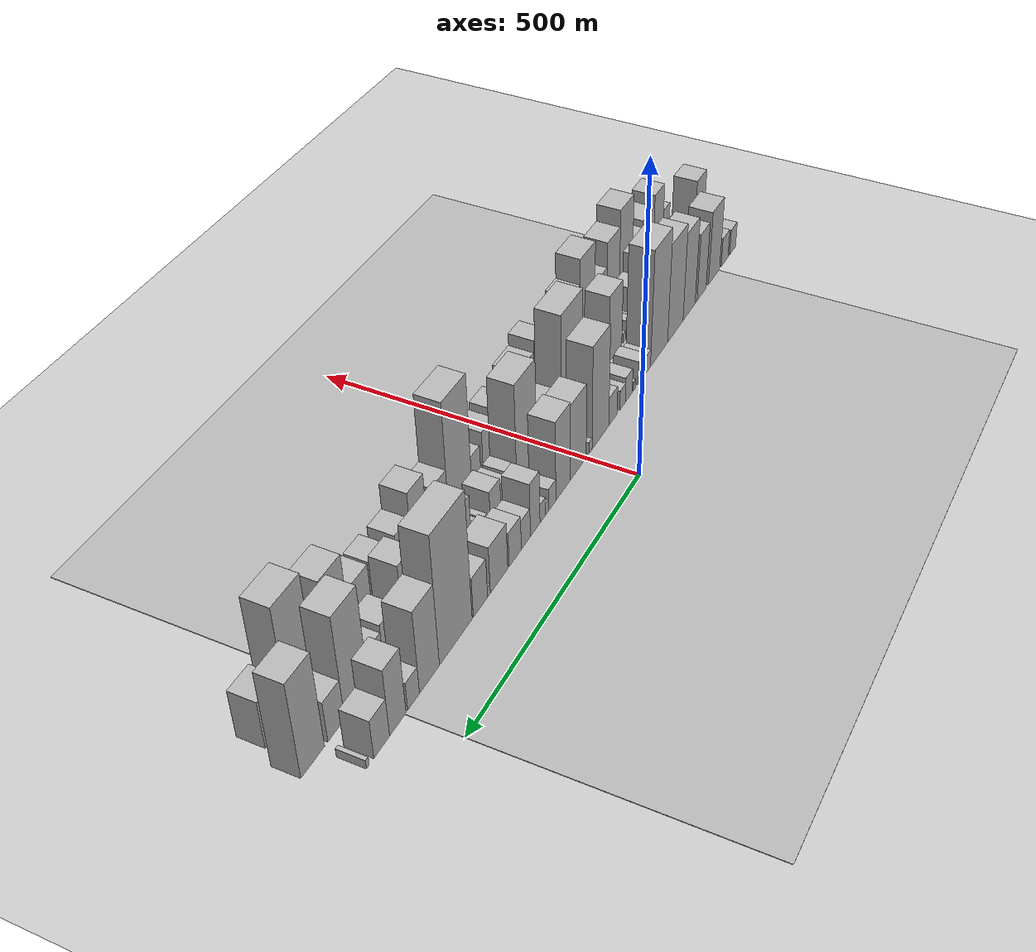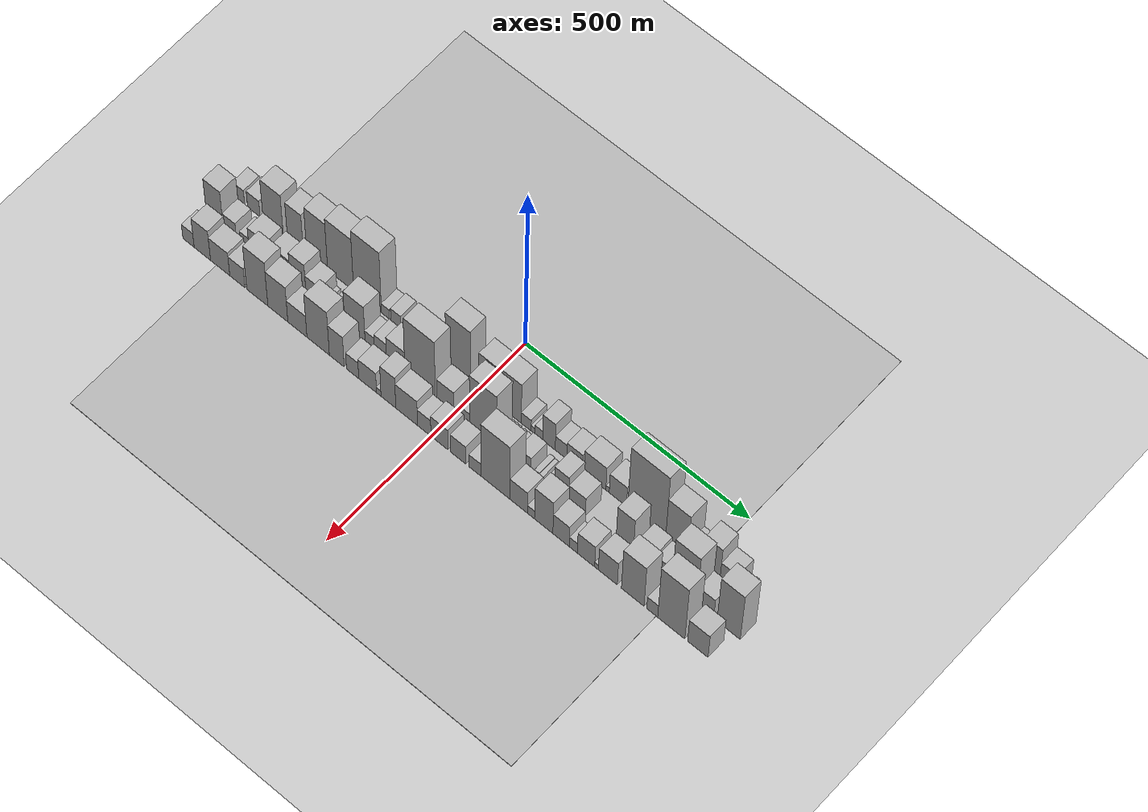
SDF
<?xml version="1.0" encoding="utf-8"?>

<sdf version="1.6">

   <world name="default">

      <gui fullscreen="0">

         <camera name="user_camera">

            <pose>-15 0 4.57585 0 0 0</pose>

            <view_controller>orbit</view_controller>

         </camera>

      </gui>

      <scene>

         <sky>

           <clouds>

             <speed>12</speed>

           </clouds>

         </sky>

         <ambient>0.4 0.4 0.4 1</ambient>

         <background>0.7 0.7 0.7 1</background>

         <shadows>1</shadows>

      </scene>

      <gravity>0 0 -9.8066</gravity>

      <magnetic_field>6e-06 2.3e-05 -4.2e-05</magnetic_field>

      <physics default="0" name="default_physics" type="ode">

         <ode>

            <solver>

               <type>quick</type>

               <iters>10</iters>

               <sor>1.0</sor>

               <use_dynamic_moi_rescaling>0</use_dynamic_moi_rescaling>

            </solver>

            <constraints>

               <cfm>0</cfm>

               <erp>0.2</erp>

               <contact_max_correcting_vel>100</contact_max_correcting_vel>

               <contact_surface_layer>0.001</contact_surface_layer>

            </constraints>

         </ode>

         <max_step_size>0.004</max_step_size>

         <real_time_factor>1</real_time_factor>

         <real_time_update_rate>250</real_time_update_rate>

      </physics>

      <light name="sun" type="directional">

         <cast_shadows>1</cast_shadows>

         <pose>0 0 10 0 0 0</pose>

         <diffuse>0.8 0.8 0.8 1</diffuse>

         <specular>0.2 0.2 0.2 1</specular>

         <attenuation>

            <range>1000</range>

            <constant>0.9</constant>

            <linear>0.01</linear>

            <quadratic>0.001</quadratic>

         </attenuation>

         <direction>-0.5 0.1 -0.9</direction>

      </light>

      <include>

         <name>ground_plane_1</name>

         <uri>model://HANNAS_ground_plane</uri>

         <pose>0 0 0  0 0 0</pose>

      </include>

      <include>

         <name>ground_plane_2</name>

         <uri>model://HANNAS_ground_plane</uri>

         <pose>100 0 0  0 0 0</pose>

      </include>

      <model name="building_1">

         <static>1</static>

         <pose frame="">100.0000 -559.6383 0 0.000000 0.000000 0.000000</pose>

         <link name="link">

            <pose frame="">0 0 24.00 0 0 0</pose>

            <collision name="collision">

               <geometry>

                  <box>

                     <size>40.0000 26.7234 48.0000</size>

                  </box>

               </geometry>

               <max_contacts>10</max_contacts>

               <surface>

                  <contact>

                     <ode/>

                  </contact>

                  <bounce/>

                  <friction>

                     <torsional>

                        <ode/>

                     </torsional>

                     <ode/>

                  </friction>

               </surface>

            </collision>

            <visual name="visual">

               <cast_shadows>0</cast_shadows>

               <geometry>

                  <box>

                     <size>40.0000 26.7234 48.0000</size>

                  </box>

               </geometry>

               <material>

                  <script>

                     <uri>model://HANNAS_wall/materials/scripts</uri>

                     <uri>model://HANNAS_wall/materials/textures</uri>

                     <name>vrc/HANNAS_wall</name>

                  </script>

               </material>

            </visual>

            <self_collide>0</self_collide>

            <enable_wind>0</enable_wind>

            <kinematic>0</kinematic>

         </link>

      </model>

      <model name="building_2">

         <static>1</static>

         <pose frame="">100.0000 -524.3369 0 0.000000 0.000000 0.000000</pose>

         <link name="link">

            <pose frame="">0 0 27.00 0 0 0</pose>

            <collision name="collision">

               <geometry>

                  <box>

                     <size>40.0000 29.8794 54.0000</size>

                  </box>

               </geometry>

               <max_contacts>10</max_contacts>

               <surface>

                  <contact>

                     <ode/>

                  </contact>

                  <bounce/>

                  <friction>

                     <torsional>

                        <ode/>

                     </torsional>

                     <ode/>

                  </friction>

               </surface>

            </collision>

            <visual name="visual">

               <cast_shadows>0</cast_shadows>

               <geometry>

                  <box>

                     <size>40.0000 29.8794 54.0000</size>

                  </box>

               </geometry>

               <material>

                  <script>

                     <uri>model://HANNAS_wall/materials/scripts</uri>

                     <uri>model://HANNAS_wall/materials/textures</uri>

                     <name>vrc/HANNAS_wall</name>

                  </script>

               </material>

            </visual>

            <self_collide>0</self_collide>

            <enable_wind>0</enable_wind>

            <kinematic>0</kinematic>

         </link>

      </model>

      <model name="building_3">

         <static>1</static>

         <pose frame="">100.0000 -478.4621 0 0.000000 0.000000 0.000000</pose>

         <link name="link">

            <pose frame="">0 0 67.50 0 0 0</pose>

            <collision name="collision">

               <geometry>

                  <box>

                     <size>40.0000 47.8702 135.0000</size>

                  </box>

               </geometry>

               <max_contacts>10</max_contacts>

               <surface>

                  <contact>

                     <ode/>

                  </contact>

                  <bounce/>

                  <friction>

                     <torsional>

                        <ode/>

                     </torsional>

                     <ode/>

                  </friction>

               </surface>

            </collision>

            <visual name="visual">

               <cast_shadows>0</cast_shadows>

               <geometry>

                  <box>

                     <size>40.0000 47.8702 135.0000</size>

                  </box>

               </geometry>

               <material>

                  <script>

                     <uri>model://HANNAS_wall/materials/scripts</uri>

                     <uri>model://HANNAS_wall/materials/textures</uri>

                     <name>vrc/HANNAS_wall</name>

                  </script>

               </material>

            </visual>

            <self_collide>0</self_collide>

            <enable_wind>0</enable_wind>

            <kinematic>0</kinematic>

         </link>

      </model>

      <model name="building_4">

         <static>1</static>

         <pose frame="">100.0000 -425.8736 0 0.000000 0.000000 0.000000</pose>

         <link name="link">

            <pose frame="">0 0 61.50 0 0 0</pose>

            <collision name="collision">

               <geometry>

                  <box>

                     <size>40.0000 37.3067 123.0000</size>

                  </box>

               </geometry>

               <max_contacts>10</max_contacts>

               <surface>

                  <contact>

                     <ode/>

                  </contact>

                  <bounce/>

                  <friction>

                     <torsional>

                        <ode/>

                     </torsional>

                     <ode/>

                  </friction>

               </surface>

            </collision>

            <visual name="visual">

               <cast_shadows>0</cast_shadows>

               <geometry>

                  <box>

                     <size>40.0000 37.3067 123.0000</size>

                  </box>

               </geometry>

               <material>

                  <script>

                     <uri>model://HANNAS_wall/materials/scripts</uri>

                     <uri>model://HANNAS_wall/materials/textures</uri>

                     <name>vrc/HANNAS_wall</name>

                  </script>

               </material>

            </visual>

            <self_collide>0</self_collide>

            <enable_wind>0</enable_wind>

            <kinematic>0</kinematic>

         </link>

      </model>

      <model name="building_5">

         <static>1</static>

         <pose frame="">100.0000 -403.0563 0 0.000000 0.000000 0.000000</pose>

         <link name="link">

            <pose frame="">0 0 9.00 0 0 0</pose>

            <collision name="collision">

               <geometry>

                  <box>

                     <size>40.0000 8.3280 18.0000</size>

                  </box>

               </geometry>

               <max_contacts>10</max_contacts>

               <surface>

                  <contact>

                     <ode/>

                  </contact>

                  <bounce/>

                  <friction>

                     <torsional>

                        <ode/>

                     </torsional>

                     <ode/>

                  </friction>

               </surface>

            </collision>

            <visual name="visual">

               <cast_shadows>0</cast_shadows>

               <geometry>

                  <box>

                     <size>40.0000 8.3280 18.0000</size>

                  </box>

               </geometry>

               <material>

                  <script>

                     <uri>model://HANNAS_wall/materials/scripts</uri>

                     <uri>model://HANNAS_wall/materials/textures</uri>

                     <name>vrc/HANNAS_wall</name>

                  </script>

               </material>

            </visual>

            <self_collide>0</self_collide>

            <enable_wind>0</enable_wind>

            <kinematic>0</kinematic>

         </link>

      </model>

      <model name="building_6">

         <static>1</static>

         <pose frame="">100.0000 -374.4395 0 0.000000 0.000000 0.000000</pose>

         <link name="link">

            <pose frame="">0 0 79.50 0 0 0</pose>

            <collision name="collision">

               <geometry>

                  <box>

                     <size>40.0000 48.9057 159.0000</size>

                  </box>

               </geometry>

               <max_contacts>10</max_contacts>

               <surface>

                  <contact>

                     <ode/>

                  </contact>

                  <bounce/>

                  <friction>

                     <torsional>

                        <ode/>

                     </torsional>

                     <ode/>

                  </friction>

               </surface>

            </collision>

            <visual name="visual">

               <cast_shadows>0</cast_shadows>

               <geometry>

                  <box>

                     <size>40.0000 48.9057 159.0000</size>

                  </box>

               </geometry>

               <material>

                  <script>

                     <uri>model://HANNAS_wall/materials/scripts</uri>

                     <uri>model://HANNAS_wall/materials/textures</uri>

                     <name>vrc/HANNAS_wall</name>

                  </script>

               </material>

            </visual>

            <self_collide>0</self_collide>

            <enable_wind>0</enable_wind>

            <kinematic>0</kinematic>

         </link>

      </model>

      <model name="building_7">

         <static>1</static>

         <pose frame="">100.0000 -319.6040 0 0.000000 0.000000 0.000000</pose>

         <link name="link">

            <pose frame="">0 0 88.50 0 0 0</pose>

            <collision name="collision">

               <geometry>

                  <box>

                     <size>40.0000 60.7652 177.0000</size>

                  </box>

               </geometry>

               <max_contacts>10</max_contacts>

               <surface>

                  <contact>

                     <ode/>

                  </contact>

                  <bounce/>

                  <friction>

                     <torsional>

                        <ode/>

                     </torsional>

                     <ode/>

                  </friction>

               </surface>

            </collision>

            <visual name="visual">

               <cast_shadows>0</cast_shadows>

               <geometry>

                  <box>

                     <size>40.0000 60.7652 177.0000</size>

                  </box>

               </geometry>

               <material>

                  <script>

                     <uri>model://HANNAS_wall/materials/scripts</uri>

                     <uri>model://HANNAS_wall/materials/textures</uri>

                     <name>vrc/HANNAS_wall</name>

                  </script>

               </material>

            </visual>

            <self_collide>0</self_collide>

            <enable_wind>0</enable_wind>

            <kinematic>0</kinematic>

         </link>

      </model>

      <model name="building_8">

         <static>1</static>

         <pose frame="">100.0000 -256.8189 0 0.000000 0.000000 0.000000</pose>

         <link name="link">

            <pose frame="">0 0 103.50 0 0 0</pose>

            <collision name="collision">

               <geometry>

                  <box>

                     <size>40.0000 64.8049 207.0000</size>

                  </box>

               </geometry>

               <max_contacts>10</max_contacts>

               <surface>

                  <contact>

                     <ode/>

                  </contact>

                  <bounce/>

                  <friction>

                     <torsional>

                        <ode/>

                     </torsional>

                     <ode/>

                  </friction>

               </surface>

            </collision>

            <visual name="visual">

               <cast_shadows>0</cast_shadows>

               <geometry>

                  <box>

                     <size>40.0000 64.8049 207.0000</size>

                  </box>

               </geometry>

               <material>

                  <script>

                     <uri>model://HANNAS_wall/materials/scripts</uri>

                     <uri>model://HANNAS_wall/materials/textures</uri>

                     <name>vrc/HANNAS_wall</name>

                  </script>

               </material>

            </visual>

            <self_collide>0</self_collide>

            <enable_wind>0</enable_wind>

            <kinematic>0</kinematic>

         </link>

      </model>

      <model name="building_9">

         <static>1</static>

         <pose frame="">100.0000 -215.1437 0 0.000000 0.000000 0.000000</pose>

         <link name="link">

            <pose frame="">0 0 16.50 0 0 0</pose>

            <collision name="collision">

               <geometry>

                  <box>

                     <size>40.0000 18.5455 33.0000</size>

                  </box>

               </geometry>

               <max_contacts>10</max_contacts>

               <surface>

                  <contact>

                     <ode/>

                  </contact>

                  <bounce/>

                  <friction>

                     <torsional>

                        <ode/>

                     </torsional>

                     <ode/>

                  </friction>

               </surface>

            </collision>

            <visual name="visual">

               <cast_shadows>0</cast_shadows>

               <geometry>

                  <box>

                     <size>40.0000 18.5455 33.0000</size>

                  </box>

               </geometry>

               <material>

                  <script>

                     <uri>model://HANNAS_wall/materials/scripts</uri>

                     <uri>model://HANNAS_wall/materials/textures</uri>

                     <name>vrc/HANNAS_wall</name>

                  </script>

               </material>

            </visual>

            <self_collide>0</self_collide>

            <enable_wind>0</enable_wind>

            <kinematic>0</kinematic>

         </link>

      </model>

      <model name="building_10">

         <static>1</static>

         <pose frame="">100.0000 -191.0404 0 0.000000 0.000000 0.000000</pose>

         <link name="link">

            <pose frame="">0 0 21.00 0 0 0</pose>

            <collision name="collision">

               <geometry>

                  <box>

                     <size>40.0000 23.6610 42.0000</size>

                  </box>

               </geometry>

               <max_contacts>10</max_contacts>

               <surface>

                  <contact>

                     <ode/>

                  </contact>

                  <bounce/>

                  <friction>

                     <torsional>

                        <ode/>

                     </torsional>

                     <ode/>

                  </friction>

               </surface>

            </collision>

            <visual name="visual">

               <cast_shadows>0</cast_shadows>

               <geometry>

                  <box>

                     <size>40.0000 23.6610 42.0000</size>

                  </box>

               </geometry>

               <material>

                  <script>

                     <uri>model://HANNAS_wall/materials/scripts</uri>

                     <uri>model://HANNAS_wall/materials/textures</uri>

                     <name>vrc/HANNAS_wall</name>

                  </script>

               </material>

            </visual>

            <self_collide>0</self_collide>

            <enable_wind>0</enable_wind>

            <kinematic>0</kinematic>

         </link>

      </model>

      <model name="building_11">

         <static>1</static>

         <pose frame="">100.0000 -165.4603 0 0.000000 0.000000 0.000000</pose>

         <link name="link">

            <pose frame="">0 0 9.00 0 0 0</pose>

            <collision name="collision">

               <geometry>

                  <box>

                     <size>40.0000 7.4993 18.0000</size>

                  </box>

               </geometry>

               <max_contacts>10</max_contacts>

               <surface>

                  <contact>

                     <ode/>

                  </contact>

                  <bounce/>

                  <friction>

                     <torsional>

                        <ode/>

                     </torsional>

                     <ode/>

                  </friction>

               </surface>

            </collision>

            <visual name="visual">

               <cast_shadows>0</cast_shadows>

               <geometry>

                  <box>

                     <size>40.0000 7.4993 18.0000</size>

                  </box>

               </geometry>

               <material>

                  <script>

                     <uri>model://HANNAS_wall/materials/scripts</uri>

                     <uri>model://HANNAS_wall/materials/textures</uri>

                     <name>vrc/HANNAS_wall</name>

                  </script>

               </material>

            </visual>

            <self_collide>0</self_collide>

            <enable_wind>0</enable_wind>

            <kinematic>0</kinematic>

         </link>

      </model>

      <model name="building_12">

         <static>1</static>

         <pose frame="">100.0000 -145.5860 0 0.000000 0.000000 0.000000</pose>

         <link name="link">

            <pose frame="">0 0 22.50 0 0 0</pose>

            <collision name="collision">

               <geometry>

                  <box>

                     <size>40.0000 24.2491 45.0000</size>

                  </box>

               </geometry>

               <max_contacts>10</max_contacts>

               <surface>

                  <contact>

                     <ode/>

                  </contact>

                  <bounce/>

                  <friction>

                     <torsional>

                        <ode/>

                     </torsional>

                     <ode/>

                  </friction>

               </surface>

            </collision>

            <visual name="visual">

               <cast_shadows>0</cast_shadows>

               <geometry>

                  <box>

                     <size>40.0000 24.2491 45.0000</size>

                  </box>

               </geometry>

               <material>

                  <script>

                     <uri>model://HANNAS_wall/materials/scripts</uri>

                     <uri>model://HANNAS_wall/materials/textures</uri>

                     <name>vrc/HANNAS_wall</name>

                  </script>

               </material>

            </visual>

            <self_collide>0</self_collide>

            <enable_wind>0</enable_wind>

            <kinematic>0</kinematic>

         </link>

      </model>

      <model name="building_13">

         <static>1</static>

         <pose frame="">100.0000 -123.6459 0 0.000000 0.000000 0.000000</pose>

         <link name="link">

            <pose frame="">0 0 18.00 0 0 0</pose>

            <collision name="collision">

               <geometry>

                  <box>

                     <size>40.0000 19.6311 36.0000</size>

                  </box>

               </geometry>

               <max_contacts>10</max_contacts>

               <surface>

                  <contact>

                     <ode/>

                  </contact>

                  <bounce/>

                  <friction>

                     <torsional>

                        <ode/>

                     </torsional>

                     <ode/>

                  </friction>

               </surface>

            </collision>

            <visual name="visual">

               <cast_shadows>0</cast_shadows>

               <geometry>

                  <box>

                     <size>40.0000 19.6311 36.0000</size>

                  </box>

               </geometry>

               <material>

                  <script>

                     <uri>model://HANNAS_wall/materials/scripts</uri>

                     <uri>model://HANNAS_wall/materials/textures</uri>

                     <name>vrc/HANNAS_wall</name>

                  </script>

               </material>

            </visual>

            <self_collide>0</self_collide>

            <enable_wind>0</enable_wind>

            <kinematic>0</kinematic>

         </link>

      </model>

      <model name="building_14">

         <static>1</static>

         <pose frame="">100.0000 -90.2637 0 0.000000 0.000000 0.000000</pose>

         <link name="link">

            <pose frame="">0 0 25.50 0 0 0</pose>

            <collision name="collision">

               <geometry>

                  <box>

                     <size>40.0000 29.1333 51.0000</size>

                  </box>

               </geometry>

               <max_contacts>10</max_contacts>

               <surface>

                  <contact>

                     <ode/>

                  </contact>

                  <bounce/>

                  <friction>

                     <torsional>

                        <ode/>

                     </torsional>

                     <ode/>

                  </friction>

               </surface>

            </collision>

            <visual name="visual">

               <cast_shadows>0</cast_shadows>

               <geometry>

                  <box>

                     <size>40.0000 29.1333 51.0000</size>

                  </box>

               </geometry>

               <material>

                  <script>

                     <uri>model://HANNAS_wall/materials/scripts</uri>

                     <uri>model://HANNAS_wall/materials/textures</uri>

                     <name>vrc/HANNAS_wall</name>

                  </script>

               </material>

            </visual>

            <self_collide>0</self_collide>

            <enable_wind>0</enable_wind>

            <kinematic>0</kinematic>

         </link>

      </model>

      <model name="building_15">

         <static>1</static>

         <pose frame="">100.0000 -47.6259 0 0.000000 0.000000 0.000000</pose>

         <link name="link">

            <pose frame="">0 0 90.00 0 0 0</pose>

            <collision name="collision">

               <geometry>

                  <box>

                     <size>40.0000 56.1424 180.0000</size>

                  </box>

               </geometry>

               <max_contacts>10</max_contacts>

               <surface>

                  <contact>

                     <ode/>

                  </contact>

                  <bounce/>

                  <friction>

                     <torsional>

                        <ode/>

                     </torsional>

                     <ode/>

                  </friction>

               </surface>

            </collision>

            <visual name="visual">

               <cast_shadows>0</cast_shadows>

               <geometry>

                  <box>

                     <size>40.0000 56.1424 180.0000</size>

                  </box>

               </geometry>

               <material>

                  <script>

                     <uri>model://HANNAS_wall/materials/scripts</uri>

                     <uri>model://HANNAS_wall/materials/textures</uri>

                     <name>vrc/HANNAS_wall</name>

                  </script>

               </material>

            </visual>

            <self_collide>0</self_collide>

            <enable_wind>0</enable_wind>

            <kinematic>0</kinematic>

         </link>

      </model>

      <model name="building_16">

         <static>1</static>

         <pose frame="">100.0000 -14.3645 0 0.000000 0.000000 0.000000</pose>

         <link name="link">

            <pose frame="">0 0 10.50 0 0 0</pose>

            <collision name="collision">

               <geometry>

                  <box>

                     <size>40.0000 10.3804 21.0000</size>

                  </box>

               </geometry>

               <max_contacts>10</max_contacts>

               <surface>

                  <contact>

                     <ode/>

                  </contact>

                  <bounce/>

                  <friction>

                     <torsional>

                        <ode/>

                     </torsional>

                     <ode/>

                  </friction>

               </surface>

            </collision>

            <visual name="visual">

               <cast_shadows>0</cast_shadows>

               <geometry>

                  <box>

                     <size>40.0000 10.3804 21.0000</size>

                  </box>

               </geometry>

               <material>

                  <script>

                     <uri>model://HANNAS_wall/materials/scripts</uri>

                     <uri>model://HANNAS_wall/materials/textures</uri>

                     <name>vrc/HANNAS_wall</name>

                  </script>

               </material>

            </visual>

            <self_collide>0</self_collide>

            <enable_wind>0</enable_wind>

            <kinematic>0</kinematic>

         </link>

      </model>

      <model name="building_17">

         <static>1</static>

         <pose frame="">100.0000 24.9637 0 0.000000 0.000000 0.000000</pose>

         <link name="link">

            <pose frame="">0 0 66.00 0 0 0</pose>

            <collision name="collision">

               <geometry>

                  <box>

                     <size>40.0000 50.2759 132.0000</size>

                  </box>

               </geometry>

               <max_contacts>10</max_contacts>

               <surface>

                  <contact>

                     <ode/>

                  </contact>

                  <bounce/>

                  <friction>

                     <torsional>

                        <ode/>

                     </torsional>

                     <ode/>

                  </friction>

               </surface>

            </collision>

            <visual name="visual">

               <cast_shadows>0</cast_shadows>

               <geometry>

                  <box>

                     <size>40.0000 50.2759 132.0000</size>

                  </box>

               </geometry>

               <material>

                  <script>

                     <uri>model://HANNAS_wall/materials/scripts</uri>

                     <uri>model://HANNAS_wall/materials/textures</uri>

                     <name>vrc/HANNAS_wall</name>

                  </script>

               </material>

            </visual>

            <self_collide>0</self_collide>

            <enable_wind>0</enable_wind>

            <kinematic>0</kinematic>

         </link>

      </model>

      <model name="building_18">

         <static>1</static>

         <pose frame="">100.0000 72.8761 0 0.000000 0.000000 0.000000</pose>

         <link name="link">

            <pose frame="">0 0 69.00 0 0 0</pose>

            <collision name="collision">

               <geometry>

                  <box>

                     <size>40.0000 45.5489 138.0000</size>

                  </box>

               </geometry>

               <max_contacts>10</max_contacts>

               <surface>

                  <contact>

                     <ode/>

                  </contact>

                  <bounce/>

                  <friction>

                     <torsional>

                        <ode/>

                     </torsional>

                     <ode/>

                  </friction>

               </surface>

            </collision>

            <visual name="visual">

               <cast_shadows>0</cast_shadows>

               <geometry>

                  <box>

                     <size>40.0000 45.5489 138.0000</size>

                  </box>

               </geometry>

               <material>

                  <script>

                     <uri>model://HANNAS_wall/materials/scripts</uri>

                     <uri>model://HANNAS_wall/materials/textures</uri>

                     <name>vrc/HANNAS_wall</name>

                  </script>

               </material>

            </visual>

            <self_collide>0</self_collide>

            <enable_wind>0</enable_wind>

            <kinematic>0</kinematic>

         </link>

      </model>

      <model name="building_19">

         <static>1</static>

         <pose frame="">100.0000 106.7918 0 0.000000 0.000000 0.000000</pose>

         <link name="link">

            <pose frame="">0 0 19.50 0 0 0</pose>

            <collision name="collision">

               <geometry>

                  <box>

                     <size>40.0000 22.2826 39.0000</size>

                  </box>

               </geometry>

               <max_contacts>10</max_contacts>

               <surface>

                  <contact>

                     <ode/>

                  </contact>

                  <bounce/>

                  <friction>

                     <torsional>

                        <ode/>

                     </torsional>

                     <ode/>

                  </friction>

               </surface>

            </collision>

            <visual name="visual">

               <cast_shadows>0</cast_shadows>

               <geometry>

                  <box>

                     <size>40.0000 22.2826 39.0000</size>

                  </box>

               </geometry>

               <material>

                  <script>

                     <uri>model://HANNAS_wall/materials/scripts</uri>

                     <uri>model://HANNAS_wall/materials/textures</uri>

                     <name>vrc/HANNAS_wall</name>

                  </script>

               </material>

            </visual>

            <self_collide>0</self_collide>

            <enable_wind>0</enable_wind>

            <kinematic>0</kinematic>

         </link>

      </model>

      <model name="building_20">

         <static>1</static>

         <pose frame="">100.0000 122.3937 0 0.000000 0.000000 0.000000</pose>

         <link name="link">

            <pose frame="">0 0 10.50 0 0 0</pose>

            <collision name="collision">

               <geometry>

                  <box>

                     <size>40.0000 8.9211 21.0000</size>

                  </box>

               </geometry>

               <max_contacts>10</max_contacts>

               <surface>

                  <contact>

                     <ode/>

                  </contact>

                  <bounce/>

                  <friction>

                     <torsional>

                        <ode/>

                     </torsional>

                     <ode/>

                  </friction>

               </surface>

            </collision>

            <visual name="visual">

               <cast_shadows>0</cast_shadows>

               <geometry>

                  <box>

                     <size>40.0000 8.9211 21.0000</size>

                  </box>

               </geometry>

               <material>

                  <script>

                     <uri>model://HANNAS_wall/materials/scripts</uri>

                     <uri>model://HANNAS_wall/materials/textures</uri>

                     <name>vrc/HANNAS_wall</name>

                  </script>

               </material>

            </visual>

            <self_collide>0</self_collide>

            <enable_wind>0</enable_wind>

            <kinematic>0</kinematic>

         </link>

      </model>

      <model name="building_21">

         <static>1</static>

         <pose frame="">100.0000 135.3229 0 0.000000 0.000000 0.000000</pose>

         <link name="link">

            <pose frame="">0 0 16.50 0 0 0</pose>

            <collision name="collision">

               <geometry>

                  <box>

                     <size>40.0000 16.9375 33.0000</size>

                  </box>

               </geometry>

               <max_contacts>10</max_contacts>

               <surface>

                  <contact>

                     <ode/>

                  </contact>

                  <bounce/>

                  <friction>

                     <torsional>

                        <ode/>

                     </torsional>

                     <ode/>

                  </friction>

               </surface>

            </collision>

            <visual name="visual">

               <cast_shadows>0</cast_shadows>

               <geometry>

                  <box>

                     <size>40.0000 16.9375 33.0000</size>

                  </box>

               </geometry>

               <material>

                  <script>

                     <uri>model://HANNAS_wall/materials/scripts</uri>

                     <uri>model://HANNAS_wall/materials/textures</uri>

                     <name>vrc/HANNAS_wall</name>

                  </script>

               </material>

            </visual>

            <self_collide>0</self_collide>

            <enable_wind>0</enable_wind>

            <kinematic>0</kinematic>

         </link>

      </model>

      <model name="building_22">

         <static>1</static>

         <pose frame="">100.0000 157.8941 0 0.000000 0.000000 0.000000</pose>

         <link name="link">

            <pose frame="">0 0 46.50 0 0 0</pose>

            <collision name="collision">

               <geometry>

                  <box>

                     <size>40.0000 28.2049 93.0000</size>

                  </box>

               </geometry>

               <max_contacts>10</max_contacts>

               <surface>

                  <contact>

                     <ode/>

                  </contact>

                  <bounce/>

                  <friction>

                     <torsional>

                        <ode/>

                     </torsional>

                     <ode/>

                  </friction>

               </surface>

            </collision>

            <visual name="visual">

               <cast_shadows>0</cast_shadows>

               <geometry>

                  <box>

                     <size>40.0000 28.2049 93.0000</size>

                  </box>

               </geometry>

               <material>

                  <script>

                     <uri>model://HANNAS_wall/materials/scripts</uri>

                     <uri>model://HANNAS_wall/materials/textures</uri>

                     <name>vrc/HANNAS_wall</name>

                  </script>

               </material>

            </visual>

            <self_collide>0</self_collide>

            <enable_wind>0</enable_wind>

            <kinematic>0</kinematic>

         </link>

      </model>

      <model name="building_23">

         <static>1</static>

         <pose frame="">100.0000 185.2162 0 0.000000 0.000000 0.000000</pose>

         <link name="link">

            <pose frame="">0 0 25.50 0 0 0</pose>

            <collision name="collision">

               <geometry>

                  <box>

                     <size>40.0000 26.4393 51.0000</size>

                  </box>

               </geometry>

               <max_contacts>10</max_contacts>

               <surface>

                  <contact>

                     <ode/>

                  </contact>

                  <bounce/>

                  <friction>

                     <torsional>

                        <ode/>

                     </torsional>

                     <ode/>

                  </friction>

               </surface>

            </collision>

            <visual name="visual">

               <cast_shadows>0</cast_shadows>

               <geometry>

                  <box>

                     <size>40.0000 26.4393 51.0000</size>

                  </box>

               </geometry>

               <material>

                  <script>

                     <uri>model://HANNAS_wall/materials/scripts</uri>

                     <uri>model://HANNAS_wall/materials/textures</uri>

                     <name>vrc/HANNAS_wall</name>

                  </script>

               </material>

            </visual>

            <self_collide>0</self_collide>

            <enable_wind>0</enable_wind>

            <kinematic>0</kinematic>

         </link>

      </model>

      <model name="building_24">

         <static>1</static>

         <pose frame="">100.0000 215.7490 0 0.000000 0.000000 0.000000</pose>

         <link name="link">

            <pose frame="">0 0 30.00 0 0 0</pose>

            <collision name="collision">

               <geometry>

                  <box>

                     <size>40.0000 34.6262 60.0000</size>

                  </box>

               </geometry>

               <max_contacts>10</max_contacts>

               <surface>

                  <contact>

                     <ode/>

                  </contact>

                  <bounce/>

                  <friction>

                     <torsional>

                        <ode/>

                     </torsional>

                     <ode/>

                  </friction>

               </surface>

            </collision>

            <visual name="visual">

               <cast_shadows>0</cast_shadows>

               <geometry>

                  <box>

                     <size>40.0000 34.6262 60.0000</size>

                  </box>

               </geometry>

               <material>

                  <script>

                     <uri>model://HANNAS_wall/materials/scripts</uri>

                     <uri>model://HANNAS_wall/materials/textures</uri>

                     <name>vrc/HANNAS_wall</name>

                  </script>

               </material>

            </visual>

            <self_collide>0</self_collide>

            <enable_wind>0</enable_wind>

            <kinematic>0</kinematic>

         </link>

      </model>

      <model name="building_25">

         <static>1</static>

         <pose frame="">100.0000 261.0581 0 0.000000 0.000000 0.000000</pose>

         <link name="link">

            <pose frame="">0 0 40.50 0 0 0</pose>

            <collision name="collision">

               <geometry>

                  <box>

                     <size>40.0000 47.9920 81.0000</size>

                  </box>

               </geometry>

               <max_contacts>10</max_contacts>

               <surface>

                  <contact>

                     <ode/>

                  </contact>

                  <bounce/>

                  <friction>

                     <torsional>

                        <ode/>

                     </torsional>

                     <ode/>

                  </friction>

               </surface>

            </collision>

            <visual name="visual">

               <cast_shadows>0</cast_shadows>

               <geometry>

                  <box>

                     <size>40.0000 47.9920 81.0000</size>

                  </box>

               </geometry>

               <material>

                  <script>

                     <uri>model://HANNAS_wall/materials/scripts</uri>

                     <uri>model://HANNAS_wall/materials/textures</uri>

                     <name>vrc/HANNAS_wall</name>

                  </script>

               </material>

            </visual>

            <self_collide>0</self_collide>

            <enable_wind>0</enable_wind>

            <kinematic>0</kinematic>

         </link>

      </model>

      <model name="building_26">

         <static>1</static>

         <pose frame="">100.0000 288.8642 0 0.000000 0.000000 0.000000</pose>

         <link name="link">

            <pose frame="">0 0 9.00 0 0 0</pose>

            <collision name="collision">

               <geometry>

                  <box>

                     <size>40.0000 7.6201 18.0000</size>

                  </box>

               </geometry>

               <max_contacts>10</max_contacts>

               <surface>

                  <contact>

                     <ode/>

                  </contact>

                  <bounce/>

                  <friction>

                     <torsional>

                        <ode/>

                     </torsional>

                     <ode/>

                  </friction>

               </surface>

            </collision>

            <visual name="visual">

               <cast_shadows>0</cast_shadows>

               <geometry>

                  <box>

                     <size>40.0000 7.6201 18.0000</size>

                  </box>

               </geometry>

               <material>

                  <script>

                     <uri>model://HANNAS_wall/materials/scripts</uri>

                     <uri>model://HANNAS_wall/materials/textures</uri>

                     <name>vrc/HANNAS_wall</name>

                  </script>

               </material>

            </visual>

            <self_collide>0</self_collide>

            <enable_wind>0</enable_wind>

            <kinematic>0</kinematic>

         </link>

      </model>

      <model name="building_27">

         <static>1</static>

         <pose frame="">100.0000 311.6634 0 0.000000 0.000000 0.000000</pose>

         <link name="link">

            <pose frame="">0 0 34.50 0 0 0</pose>

            <collision name="collision">

               <geometry>

                  <box>

                     <size>40.0000 37.9783 69.0000</size>

                  </box>

               </geometry>

               <max_contacts>10</max_contacts>

               <surface>

                  <contact>

                     <ode/>

                  </contact>

                  <bounce/>

                  <friction>

                     <torsional>

                        <ode/>

                     </torsional>

                     <ode/>

                  </friction>

               </surface>

            </collision>

            <visual name="visual">

               <cast_shadows>0</cast_shadows>

               <geometry>

                  <box>

                     <size>40.0000 37.9783 69.0000</size>

                  </box>

               </geometry>

               <material>

                  <script>

                     <uri>model://HANNAS_wall/materials/scripts</uri>

                     <uri>model://HANNAS_wall/materials/textures</uri>

                     <name>vrc/HANNAS_wall</name>

                  </script>

               </material>

            </visual>

            <self_collide>0</self_collide>

            <enable_wind>0</enable_wind>

            <kinematic>0</kinematic>

         </link>

      </model>

      <model name="building_28">

         <static>1</static>

         <pose frame="">100.0000 375.5406 0 0.000000 0.000000 0.000000</pose>

         <link name="link">

            <pose frame="">0 0 109.50 0 0 0</pose>

            <collision name="collision">

               <geometry>

                  <box>

                     <size>40.0000 83.7762 219.0000</size>

                  </box>

               </geometry>

               <max_contacts>10</max_contacts>

               <surface>

                  <contact>

                     <ode/>

                  </contact>

                  <bounce/>

                  <friction>

                     <torsional>

                        <ode/>

                     </torsional>

                     <ode/>

                  </friction>

               </surface>

            </collision>

            <visual name="visual">

               <cast_shadows>0</cast_shadows>

               <geometry>

                  <box>

                     <size>40.0000 83.7762 219.0000</size>

                  </box>

               </geometry>

               <material>

                  <script>

                     <uri>model://HANNAS_wall/materials/scripts</uri>

                     <uri>model://HANNAS_wall/materials/textures</uri>

                     <name>vrc/HANNAS_wall</name>

                  </script>

               </material>

            </visual>

            <self_collide>0</self_collide>

            <enable_wind>0</enable_wind>

            <kinematic>0</kinematic>

         </link>

      </model>

      <model name="building_29">

         <static>1</static>

         <pose frame="">100.0000 441.6724 0 0.000000 0.000000 0.000000</pose>

         <link name="link">

            <pose frame="">0 0 70.50 0 0 0</pose>

            <collision name="collision">

               <geometry>

                  <box>

                     <size>40.0000 48.4873 141.0000</size>

                  </box>

               </geometry>

               <max_contacts>10</max_contacts>

               <surface>

                  <contact>

                     <ode/>

                  </contact>

                  <bounce/>

                  <friction>

                     <torsional>

                        <ode/>

                     </torsional>

                     <ode/>

                  </friction>

               </surface>

            </collision>

            <visual name="visual">

               <cast_shadows>0</cast_shadows>

               <geometry>

                  <box>

                     <size>40.0000 48.4873 141.0000</size>

                  </box>

               </geometry>

               <material>

                  <script>

                     <uri>model://HANNAS_wall/materials/scripts</uri>

                     <uri>model://HANNAS_wall/materials/textures</uri>

                     <name>vrc/HANNAS_wall</name>

                  </script>

               </material>

            </visual>

            <self_collide>0</self_collide>

            <enable_wind>0</enable_wind>

            <kinematic>0</kinematic>

         </link>

      </model>

      <model name="building_30">

         <static>1</static>

         <pose frame="">100.0000 479.9010 0 0.000000 0.000000 0.000000</pose>

         <link name="link">

            <pose frame="">0 0 24.00 0 0 0</pose>

            <collision name="collision">

               <geometry>

                  <box>

                     <size>40.0000 27.9699 48.0000</size>

                  </box>

               </geometry>

               <max_contacts>10</max_contacts>

               <surface>

                  <contact>

                     <ode/>

                  </contact>

                  <bounce/>

                  <friction>

                     <torsional>

                        <ode/>

                     </torsional>

                     <ode/>

                  </friction>

               </surface>

            </collision>

            <visual name="visual">

               <cast_shadows>0</cast_shadows>

               <geometry>

                  <box>

                     <size>40.0000 27.9699 48.0000</size>

                  </box>

               </geometry>

               <material>

                  <script>

                     <uri>model://HANNAS_wall/materials/scripts</uri>

                     <uri>model://HANNAS_wall/materials/textures</uri>

                     <name>vrc/HANNAS_wall</name>

                  </script>

               </material>

            </visual>

            <self_collide>0</self_collide>

            <enable_wind>0</enable_wind>

            <kinematic>0</kinematic>

         </link>

      </model>

      <model name="building_31">

         <static>1</static>

         <pose frame="">100.0000 516.8351 0 0.000000 0.000000 0.000000</pose>

         <link name="link">

            <pose frame="">0 0 57.00 0 0 0</pose>

            <collision name="collision">

               <geometry>

                  <box>

                     <size>40.0000 37.8981 114.0000</size>

                  </box>

               </geometry>

               <max_contacts>10</max_contacts>

               <surface>

                  <contact>

                     <ode/>

                  </contact>

                  <bounce/>

                  <friction>

                     <torsional>

                        <ode/>

                     </torsional>

                     <ode/>

                  </friction>

               </surface>

            </collision>

            <visual name="visual">

               <cast_shadows>0</cast_shadows>

               <geometry>

                  <box>

                     <size>40.0000 37.8981 114.0000</size>

                  </box>

               </geometry>

               <material>

                  <script>

                     <uri>model://HANNAS_wall/materials/scripts</uri>

                     <uri>model://HANNAS_wall/materials/textures</uri>

                     <name>vrc/HANNAS_wall</name>

                  </script>

               </material>

            </visual>

            <self_collide>0</self_collide>

            <enable_wind>0</enable_wind>

            <kinematic>0</kinematic>

         </link>

      </model>

      <model name="building_32">

         <static>1</static>

         <pose frame="">100.0000 553.6374 0 0.000000 0.000000 0.000000</pose>

         <link name="link">

            <pose frame="">0 0 33.00 0 0 0</pose>

            <collision name="collision">

               <geometry>

                  <box>

                     <size>40.0000 35.7065 66.0000</size>

                  </box>

               </geometry>

               <max_contacts>10</max_contacts>

               <surface>

                  <contact>

                     <ode/>

                  </contact>

                  <bounce/>

                  <friction>

                     <torsional>

                        <ode/>

                     </torsional>

                     <ode/>

                  </friction>

               </surface>

            </collision>

            <visual name="visual">

               <cast_shadows>0</cast_shadows>

               <geometry>

                  <box>

                     <size>40.0000 35.7065 66.0000</size>

                  </box>

               </geometry>

               <material>

                  <script>

                     <uri>model://HANNAS_wall/materials/scripts</uri>

                     <uri>model://HANNAS_wall/materials/textures</uri>

                     <name>vrc/HANNAS_wall</name>

                  </script>

               </material>

            </visual>

            <self_collide>0</self_collide>

            <enable_wind>0</enable_wind>

            <kinematic>0</kinematic>

         </link>

      </model>

      <model name="building_33">

         <static>1</static>

         <pose frame="">100.0000 584.5289 0 0.000000 0.000000 0.000000</pose>

         <link name="link">

            <pose frame="">0 0 7.50 0 0 0</pose>

            <collision name="collision">

               <geometry>

                  <box>

                     <size>40.0000 6.0766 15.0000</size>

                  </box>

               </geometry>

               <max_contacts>10</max_contacts>

               <surface>

                  <contact>

                     <ode/>

                  </contact>

                  <bounce/>

                  <friction>

                     <torsional>

                        <ode/>

                     </torsional>

                     <ode/>

                  </friction>

               </surface>

            </collision>

            <visual name="visual">

               <cast_shadows>0</cast_shadows>

               <geometry>

                  <box>

                     <size>40.0000 6.0766 15.0000</size>

                  </box>

               </geometry>

               <material>

                  <script>

                     <uri>model://HANNAS_wall/materials/scripts</uri>

                     <uri>model://HANNAS_wall/materials/textures</uri>

                     <name>vrc/HANNAS_wall</name>

                  </script>

               </material>

            </visual>

            <self_collide>0</self_collide>

            <enable_wind>0</enable_wind>

            <kinematic>0</kinematic>

         </link>

      </model>

      <model name="building_34">

         <static>1</static>

         <pose frame="">160.0000 -560.1067 0 0.000000 0.000000 0.000000</pose>

         <link name="link">

            <pose frame="">0 0 63.00 0 0 0</pose>

            <collision name="collision">

               <geometry>

                  <box>

                     <size>40.0000 39.7866 126.0000</size>

                  </box>

               </geometry>

               <max_contacts>10</max_contacts>

               <surface>

                  <contact>

                     <ode/>

                  </contact>

                  <bounce/>

                  <friction>

                     <torsional>

                        <ode/>

                     </torsional>

                     <ode/>

                  </friction>

               </surface>

            </collision>

            <visual name="visual">

               <cast_shadows>0</cast_shadows>

               <geometry>

                  <box>

                     <size>40.0000 39.7866 126.0000</size>

                  </box>

               </geometry>

               <material>

                  <script>

                     <uri>model://HANNAS_wall/materials/scripts</uri>

                     <uri>model://HANNAS_wall/materials/textures</uri>

                     <name>vrc/HANNAS_wall</name>

                  </script>

               </material>

            </visual>

            <self_collide>0</self_collide>

            <enable_wind>0</enable_wind>

            <kinematic>0</kinematic>

         </link>

      </model>

      <model name="building_35">

         <static>1</static>

         <pose frame="">160.0000 -524.6617 0 0.000000 0.000000 0.000000</pose>

         <link name="link">

            <pose frame="">0 0 27.00 0 0 0</pose>

            <collision name="collision">

               <geometry>

                  <box>

                     <size>40.0000 31.1033 54.0000</size>

                  </box>

               </geometry>

               <max_contacts>10</max_contacts>

               <surface>

                  <contact>

                     <ode/>

                  </contact>

                  <bounce/>

                  <friction>

                     <torsional>

                        <ode/>

                     </torsional>

                     <ode/>

                  </friction>

               </surface>

            </collision>

            <visual name="visual">

               <cast_shadows>0</cast_shadows>

               <geometry>

                  <box>

                     <size>40.0000 31.1033 54.0000</size>

                  </box>

               </geometry>

               <material>

                  <script>

                     <uri>model://HANNAS_wall/materials/scripts</uri>

                     <uri>model://HANNAS_wall/materials/textures</uri>

                     <name>vrc/HANNAS_wall</name>

                  </script>

               </material>

            </visual>

            <self_collide>0</self_collide>

            <enable_wind>0</enable_wind>

            <kinematic>0</kinematic>

         </link>

      </model>

      <model name="building_36">

         <static>1</static>

         <pose frame="">160.0000 -489.6684 0 0.000000 0.000000 0.000000</pose>

         <link name="link">

            <pose frame="">0 0 19.50 0 0 0</pose>

            <collision name="collision">

               <geometry>

                  <box>

                     <size>40.0000 20.8833 39.0000</size>

                  </box>

               </geometry>

               <max_contacts>10</max_contacts>

               <surface>

                  <contact>

                     <ode/>

                  </contact>

                  <bounce/>

                  <friction>

                     <torsional>

                        <ode/>

                     </torsional>

                     <ode/>

                  </friction>

               </surface>

            </collision>

            <visual name="visual">

               <cast_shadows>0</cast_shadows>

               <geometry>

                  <box>

                     <size>40.0000 20.8833 39.0000</size>

                  </box>

               </geometry>

               <material>

                  <script>

                     <uri>model://HANNAS_wall/materials/scripts</uri>

                     <uri>model://HANNAS_wall/materials/textures</uri>

                     <name>vrc/HANNAS_wall</name>

                  </script>

               </material>

            </visual>

            <self_collide>0</self_collide>

            <enable_wind>0</enable_wind>

            <kinematic>0</kinematic>

         </link>

      </model>

      <model name="building_37">

         <static>1</static>

         <pose frame="">160.0000 -457.3704 0 0.000000 0.000000 0.000000</pose>

         <link name="link">

            <pose frame="">0 0 37.50 0 0 0</pose>

            <collision name="collision">

               <geometry>

                  <box>

                     <size>40.0000 43.7128 75.0000</size>

                  </box>

               </geometry>

               <max_contacts>10</max_contacts>

               <surface>

                  <contact>

                     <ode/>

                  </contact>

                  <bounce/>

                  <friction>

                     <torsional>

                        <ode/>

                     </torsional>

                     <ode/>

                  </friction>

               </surface>

            </collision>

            <visual name="visual">

               <cast_shadows>0</cast_shadows>

               <geometry>

                  <box>

                     <size>40.0000 43.7128 75.0000</size>

                  </box>

               </geometry>

               <material>

                  <script>

                     <uri>model://HANNAS_wall/materials/scripts</uri>

                     <uri>model://HANNAS_wall/materials/textures</uri>

                     <name>vrc/HANNAS_wall</name>

                  </script>

               </material>

            </visual>

            <self_collide>0</self_collide>

            <enable_wind>0</enable_wind>

            <kinematic>0</kinematic>

         </link>

      </model>

      <model name="building_38">

         <static>1</static>

         <pose frame="">160.0000 -403.6796 0 0.000000 0.000000 0.000000</pose>

         <link name="link">

            <pose frame="">0 0 37.50 0 0 0</pose>

            <collision name="collision">

               <geometry>

                  <box>

                     <size>40.0000 43.6689 75.0000</size>

                  </box>

               </geometry>

               <max_contacts>10</max_contacts>

               <surface>

                  <contact>

                     <ode/>

                  </contact>

                  <bounce/>

                  <friction>

                     <torsional>

                        <ode/>

                     </torsional>

                     <ode/>

                  </friction>

               </surface>

            </collision>

            <visual name="visual">

               <cast_shadows>0</cast_shadows>

               <geometry>

                  <box>

                     <size>40.0000 43.6689 75.0000</size>

                  </box>

               </geometry>

               <material>

                  <script>

                     <uri>model://HANNAS_wall/materials/scripts</uri>

                     <uri>model://HANNAS_wall/materials/textures</uri>

                     <name>vrc/HANNAS_wall</name>

                  </script>

               </material>

            </visual>

            <self_collide>0</self_collide>

            <enable_wind>0</enable_wind>

            <kinematic>0</kinematic>

         </link>

      </model>

      <model name="building_39">

         <static>1</static>

         <pose frame="">160.0000 -363.4628 0 0.000000 0.000000 0.000000</pose>

         <link name="link">

            <pose frame="">0 0 51.00 0 0 0</pose>

            <collision name="collision">

               <geometry>

                  <box>

                     <size>40.0000 36.7647 102.0000</size>

                  </box>

               </geometry>

               <max_contacts>10</max_contacts>

               <surface>

                  <contact>

                     <ode/>

                  </contact>

                  <bounce/>

                  <friction>

                     <torsional>

                        <ode/>

                     </torsional>

                     <ode/>

                  </friction>

               </surface>

            </collision>

            <visual name="visual">

               <cast_shadows>0</cast_shadows>

               <geometry>

                  <box>

                     <size>40.0000 36.7647 102.0000</size>

                  </box>

               </geometry>

               <material>

                  <script>

                     <uri>model://HANNAS_wall/materials/scripts</uri>

                     <uri>model://HANNAS_wall/materials/textures</uri>

                     <name>vrc/HANNAS_wall</name>

                  </script>

               </material>

            </visual>

            <self_collide>0</self_collide>

            <enable_wind>0</enable_wind>

            <kinematic>0</kinematic>

         </link>

      </model>

      <model name="building_40">

         <static>1</static>

         <pose frame="">160.0000 -327.2584 0 0.000000 0.000000 0.000000</pose>

         <link name="link">

            <pose frame="">0 0 33.00 0 0 0</pose>

            <collision name="collision">

               <geometry>

                  <box>

                     <size>40.0000 35.6440 66.0000</size>

                  </box>

               </geometry>

               <max_contacts>10</max_contacts>

               <surface>

                  <contact>

                     <ode/>

                  </contact>

                  <bounce/>

                  <friction>

                     <torsional>

                        <ode/>

                     </torsional>

                     <ode/>

                  </friction>

               </surface>

            </collision>

            <visual name="visual">

               <cast_shadows>0</cast_shadows>

               <geometry>

                  <box>

                     <size>40.0000 35.6440 66.0000</size>

                  </box>

               </geometry>

               <material>

                  <script>

                     <uri>model://HANNAS_wall/materials/scripts</uri>

                     <uri>model://HANNAS_wall/materials/textures</uri>

                     <name>vrc/HANNAS_wall</name>

                  </script>

               </material>

            </visual>

            <self_collide>0</self_collide>

            <enable_wind>0</enable_wind>

            <kinematic>0</kinematic>

         </link>

      </model>

      <model name="building_41">

         <static>1</static>

         <pose frame="">160.0000 -304.5331 0 0.000000 0.000000 0.000000</pose>

         <link name="link">

            <pose frame="">0 0 10.50 0 0 0</pose>

            <collision name="collision">

               <geometry>

                  <box>

                     <size>40.0000 9.8067 21.0000</size>

                  </box>

               </geometry>

               <max_contacts>10</max_contacts>

               <surface>

                  <contact>

                     <ode/>

                  </contact>

                  <bounce/>

                  <friction>

                     <torsional>

                        <ode/>

                     </torsional>

                     <ode/>

                  </friction>

               </surface>

            </collision>

            <visual name="visual">

               <cast_shadows>0</cast_shadows>

               <geometry>

                  <box>

                     <size>40.0000 9.8067 21.0000</size>

                  </box>

               </geometry>

               <material>

                  <script>

                     <uri>model://HANNAS_wall/materials/scripts</uri>

                     <uri>model://HANNAS_wall/materials/textures</uri>

                     <name>vrc/HANNAS_wall</name>

                  </script>

               </material>

            </visual>

            <self_collide>0</self_collide>

            <enable_wind>0</enable_wind>

            <kinematic>0</kinematic>

         </link>

      </model>

      <model name="building_42">

         <static>1</static>

         <pose frame="">160.0000 -281.1863 0 0.000000 0.000000 0.000000</pose>

         <link name="link">

            <pose frame="">0 0 16.50 0 0 0</pose>

            <collision name="collision">

               <geometry>

                  <box>

                     <size>40.0000 16.8869 33.0000</size>

                  </box>

               </geometry>

               <max_contacts>10</max_contacts>

               <surface>

                  <contact>

                     <ode/>

                  </contact>

                  <bounce/>

                  <friction>

                     <torsional>

                        <ode/>

                     </torsional>

                     <ode/>

                  </friction>

               </surface>

            </collision>

            <visual name="visual">

               <cast_shadows>0</cast_shadows>

               <geometry>

                  <box>

                     <size>40.0000 16.8869 33.0000</size>

                  </box>

               </geometry>

               <material>

                  <script>

                     <uri>model://HANNAS_wall/materials/scripts</uri>

                     <uri>model://HANNAS_wall/materials/textures</uri>

                     <name>vrc/HANNAS_wall</name>

                  </script>

               </material>

            </visual>

            <self_collide>0</self_collide>

            <enable_wind>0</enable_wind>

            <kinematic>0</kinematic>

         </link>

      </model>

      <model name="building_43">

         <static>1</static>

         <pose frame="">160.0000 -264.1302 0 0.000000 0.000000 0.000000</pose>

         <link name="link">

            <pose frame="">0 0 9.00 0 0 0</pose>

            <collision name="collision">

               <geometry>

                  <box>

                     <size>40.0000 7.2255 18.0000</size>

                  </box>

               </geometry>

               <max_contacts>10</max_contacts>

               <surface>

                  <contact>

                     <ode/>

                  </contact>

                  <bounce/>

                  <friction>

                     <torsional>

                        <ode/>

                     </torsional>

                     <ode/>

                  </friction>

               </surface>

            </collision>

            <visual name="visual">

               <cast_shadows>0</cast_shadows>

               <geometry>

                  <box>

                     <size>40.0000 7.2255 18.0000</size>

                  </box>

               </geometry>

               <material>

                  <script>

                     <uri>model://HANNAS_wall/materials/scripts</uri>

                     <uri>model://HANNAS_wall/materials/textures</uri>

                     <name>vrc/HANNAS_wall</name>

                  </script>

               </material>

            </visual>

            <self_collide>0</self_collide>

            <enable_wind>0</enable_wind>

            <kinematic>0</kinematic>

         </link>

      </model>

      <model name="building_44">

         <static>1</static>

         <pose frame="">160.0000 -231.0679 0 0.000000 0.000000 0.000000</pose>

         <link name="link">

            <pose frame="">0 0 60.00 0 0 0</pose>

            <collision name="collision">

               <geometry>

                  <box>

                     <size>40.0000 46.8989 120.0000</size>

                  </box>

               </geometry>

               <max_contacts>10</max_contacts>

               <surface>

                  <contact>

                     <ode/>

                  </contact>

                  <bounce/>

                  <friction>

                     <torsional>

                        <ode/>

                     </torsional>

                     <ode/>

                  </friction>

               </surface>

            </collision>

            <visual name="visual">

               <cast_shadows>0</cast_shadows>

               <geometry>

                  <box>

                     <size>40.0000 46.8989 120.0000</size>

                  </box>

               </geometry>

               <material>

                  <script>

                     <uri>model://HANNAS_wall/materials/scripts</uri>

                     <uri>model://HANNAS_wall/materials/textures</uri>

                     <name>vrc/HANNAS_wall</name>

                  </script>

               </material>

            </visual>

            <self_collide>0</self_collide>

            <enable_wind>0</enable_wind>

            <kinematic>0</kinematic>

         </link>

      </model>

      <model name="building_45">

         <static>1</static>

         <pose frame="">160.0000 -196.9596 0 0.000000 0.000000 0.000000</pose>

         <link name="link">

            <pose frame="">0 0 19.50 0 0 0</pose>

            <collision name="collision">

               <geometry>

                  <box>

                     <size>40.0000 21.3179 39.0000</size>

                  </box>

               </geometry>

               <max_contacts>10</max_contacts>

               <surface>

                  <contact>

                     <ode/>

                  </contact>

                  <bounce/>

                  <friction>

                     <torsional>

                        <ode/>

                     </torsional>

                     <ode/>

                  </friction>

               </surface>

            </collision>

            <visual name="visual">

               <cast_shadows>0</cast_shadows>

               <geometry>

                  <box>

                     <size>40.0000 21.3179 39.0000</size>

                  </box>

               </geometry>

               <material>

                  <script>

                     <uri>model://HANNAS_wall/materials/scripts</uri>

                     <uri>model://HANNAS_wall/materials/textures</uri>

                     <name>vrc/HANNAS_wall</name>

                  </script>

               </material>

            </visual>

            <self_collide>0</self_collide>

            <enable_wind>0</enable_wind>

            <kinematic>0</kinematic>

         </link>

      </model>

      <model name="building_46">

         <static>1</static>

         <pose frame="">160.0000 -172.2539 0 0.000000 0.000000 0.000000</pose>

         <link name="link">

            <pose frame="">0 0 25.50 0 0 0</pose>

            <collision name="collision">

               <geometry>

                  <box>

                     <size>40.0000 28.0935 51.0000</size>

                  </box>

               </geometry>

               <max_contacts>10</max_contacts>

               <surface>

                  <contact>

                     <ode/>

                  </contact>

                  <bounce/>

                  <friction>

                     <torsional>

                        <ode/>

                     </torsional>

                     <ode/>

                  </friction>

               </surface>

            </collision>

            <visual name="visual">

               <cast_shadows>0</cast_shadows>

               <geometry>

                  <box>

                     <size>40.0000 28.0935 51.0000</size>

                  </box>

               </geometry>

               <material>

                  <script>

                     <uri>model://HANNAS_wall/materials/scripts</uri>

                     <uri>model://HANNAS_wall/materials/textures</uri>

                     <name>vrc/HANNAS_wall</name>

                  </script>

               </material>

            </visual>

            <self_collide>0</self_collide>

            <enable_wind>0</enable_wind>

            <kinematic>0</kinematic>

         </link>

      </model>

      <model name="building_47">

         <static>1</static>

         <pose frame="">160.0000 -136.9309 0 0.000000 0.000000 0.000000</pose>

         <link name="link">

            <pose frame="">0 0 37.50 0 0 0</pose>

            <collision name="collision">

               <geometry>

                  <box>

                     <size>40.0000 42.5526 75.0000</size>

                  </box>

               </geometry>

               <max_contacts>10</max_contacts>

               <surface>

                  <contact>

                     <ode/>

                  </contact>

                  <bounce/>

                  <friction>

                     <torsional>

                        <ode/>

                     </torsional>

                     <ode/>

                  </friction>

               </surface>

            </collision>

            <visual name="visual">

               <cast_shadows>0</cast_shadows>

               <geometry>

                  <box>

                     <size>40.0000 42.5526 75.0000</size>

                  </box>

               </geometry>

               <material>

                  <script>

                     <uri>model://HANNAS_wall/materials/scripts</uri>

                     <uri>model://HANNAS_wall/materials/textures</uri>

                     <name>vrc/HANNAS_wall</name>

                  </script>

               </material>

            </visual>

            <self_collide>0</self_collide>

            <enable_wind>0</enable_wind>

            <kinematic>0</kinematic>

         </link>

      </model>

      <model name="building_48">

         <static>1</static>

         <pose frame="">160.0000 -80.7195 0 0.000000 0.000000 0.000000</pose>

         <link name="link">

            <pose frame="">0 0 97.50 0 0 0</pose>

            <collision name="collision">

               <geometry>

                  <box>

                     <size>40.0000 69.8701 195.0000</size>

                  </box>

               </geometry>

               <max_contacts>10</max_contacts>

               <surface>

                  <contact>

                     <ode/>

                  </contact>

                  <bounce/>

                  <friction>

                     <torsional>

                        <ode/>

                     </torsional>

                     <ode/>

                  </friction>

               </surface>

            </collision>

            <visual name="visual">

               <cast_shadows>0</cast_shadows>

               <geometry>

                  <box>

                     <size>40.0000 69.8701 195.0000</size>

                  </box>

               </geometry>

               <material>

                  <script>

                     <uri>model://HANNAS_wall/materials/scripts</uri>

                     <uri>model://HANNAS_wall/materials/textures</uri>

                     <name>vrc/HANNAS_wall</name>

                  </script>

               </material>

            </visual>

            <self_collide>0</self_collide>

            <enable_wind>0</enable_wind>

            <kinematic>0</kinematic>

         </link>

      </model>

      <model name="building_49">

         <static>1</static>

         <pose frame="">160.0000 -23.3285 0 0.000000 0.000000 0.000000</pose>

         <link name="link">

            <pose frame="">0 0 34.50 0 0 0</pose>

            <collision name="collision">

               <geometry>

                  <box>

                     <size>40.0000 38.9121 69.0000</size>

                  </box>

               </geometry>

               <max_contacts>10</max_contacts>

               <surface>

                  <contact>

                     <ode/>

                  </contact>

                  <bounce/>

                  <friction>

                     <torsional>

                        <ode/>

                     </torsional>

                     <ode/>

                  </friction>

               </surface>

            </collision>

            <visual name="visual">

               <cast_shadows>0</cast_shadows>

               <geometry>

                  <box>

                     <size>40.0000 38.9121 69.0000</size>

                  </box>

               </geometry>

               <material>

                  <script>

                     <uri>model://HANNAS_wall/materials/scripts</uri>

                     <uri>model://HANNAS_wall/materials/textures</uri>

                     <name>vrc/HANNAS_wall</name>

                  </script>

               </material>

            </visual>

            <self_collide>0</self_collide>

            <enable_wind>0</enable_wind>

            <kinematic>0</kinematic>

         </link>

      </model>

      <model name="building_50">

         <static>1</static>

         <pose frame="">160.0000 8.7898 0 0.000000 0.000000 0.000000</pose>

         <link name="link">

            <pose frame="">0 0 9.00 0 0 0</pose>

            <collision name="collision">

               <geometry>

                  <box>

                     <size>40.0000 7.3244 18.0000</size>

                  </box>

               </geometry>

               <max_contacts>10</max_contacts>

               <surface>

                  <contact>

                     <ode/>

                  </contact>

                  <bounce/>

                  <friction>

                     <torsional>

                        <ode/>

                     </torsional>

                     <ode/>

                  </friction>

               </surface>

            </collision>

            <visual name="visual">

               <cast_shadows>0</cast_shadows>

               <geometry>

                  <box>

                     <size>40.0000 7.3244 18.0000</size>

                  </box>

               </geometry>

               <material>

                  <script>

                     <uri>model://HANNAS_wall/materials/scripts</uri>

                     <uri>model://HANNAS_wall/materials/textures</uri>

                     <name>vrc/HANNAS_wall</name>

                  </script>

               </material>

            </visual>

            <self_collide>0</self_collide>

            <enable_wind>0</enable_wind>

            <kinematic>0</kinematic>

         </link>

      </model>

      <model name="building_51">

         <static>1</static>

         <pose frame="">160.0000 22.3346 0 0.000000 0.000000 0.000000</pose>

         <link name="link">

            <pose frame="">0 0 19.50 0 0 0</pose>

            <collision name="collision">

               <geometry>

                  <box>

                     <size>40.0000 19.7651 39.0000</size>

                  </box>

               </geometry>

               <max_contacts>10</max_contacts>

               <surface>

                  <contact>

                     <ode/>

                  </contact>

                  <bounce/>

                  <friction>

                     <torsional>

                        <ode/>

                     </torsional>

                     <ode/>

                  </friction>

               </surface>

            </collision>

            <visual name="visual">

               <cast_shadows>0</cast_shadows>

               <geometry>

                  <box>

                     <size>40.0000 19.7651 39.0000</size>

                  </box>

               </geometry>

               <material>

                  <script>

                     <uri>model://HANNAS_wall/materials/scripts</uri>

                     <uri>model://HANNAS_wall/materials/textures</uri>

                     <name>vrc/HANNAS_wall</name>

                  </script>

               </material>

            </visual>

            <self_collide>0</self_collide>

            <enable_wind>0</enable_wind>

            <kinematic>0</kinematic>

         </link>

      </model>

      <model name="building_52">

         <static>1</static>

         <pose frame="">160.0000 62.6329 0 0.000000 0.000000 0.000000</pose>

         <link name="link">

            <pose frame="">0 0 88.50 0 0 0</pose>

            <collision name="collision">

               <geometry>

                  <box>

                     <size>40.0000 60.8315 177.0000</size>

                  </box>

               </geometry>

               <max_contacts>10</max_contacts>

               <surface>

                  <contact>

                     <ode/>

                  </contact>

                  <bounce/>

                  <friction>

                     <torsional>

                        <ode/>

                     </torsional>

                     <ode/>

                  </friction>

               </surface>

            </collision>

            <visual name="visual">

               <cast_shadows>0</cast_shadows>

               <geometry>

                  <box>

                     <size>40.0000 60.8315 177.0000</size>

                  </box>

               </geometry>

               <material>

                  <script>

                     <uri>model://HANNAS_wall/materials/scripts</uri>

                     <uri>model://HANNAS_wall/materials/textures</uri>

                     <name>vrc/HANNAS_wall</name>

                  </script>

               </material>

            </visual>

            <self_collide>0</self_collide>

            <enable_wind>0</enable_wind>

            <kinematic>0</kinematic>

         </link>

      </model>

      <model name="building_53">

         <static>1</static>

         <pose frame="">160.0000 103.6001 0 0.000000 0.000000 0.000000</pose>

         <link name="link">

            <pose frame="">0 0 21.00 0 0 0</pose>

            <collision name="collision">

               <geometry>

                  <box>

                     <size>40.0000 21.1028 42.0000</size>

                  </box>

               </geometry>

               <max_contacts>10</max_contacts>

               <surface>

                  <contact>

                     <ode/>

                  </contact>

                  <bounce/>

                  <friction>

                     <torsional>

                        <ode/>

                     </torsional>

                     <ode/>

                  </friction>

               </surface>

            </collision>

            <visual name="visual">

               <cast_shadows>0</cast_shadows>

               <geometry>

                  <box>

                     <size>40.0000 21.1028 42.0000</size>

                  </box>

               </geometry>

               <material>

                  <script>

                     <uri>model://HANNAS_wall/materials/scripts</uri>

                     <uri>model://HANNAS_wall/materials/textures</uri>

                     <name>vrc/HANNAS_wall</name>

                  </script>

               </material>

            </visual>

            <self_collide>0</self_collide>

            <enable_wind>0</enable_wind>

            <kinematic>0</kinematic>

         </link>

      </model>

      <model name="building_54">

         <static>1</static>

         <pose frame="">160.0000 129.7369 0 0.000000 0.000000 0.000000</pose>

         <link name="link">

            <pose frame="">0 0 21.00 0 0 0</pose>

            <collision name="collision">

               <geometry>

                  <box>

                     <size>40.0000 21.1707 42.0000</size>

                  </box>

               </geometry>

               <max_contacts>10</max_contacts>

               <surface>

                  <contact>

                     <ode/>

                  </contact>

                  <bounce/>

                  <friction>

                     <torsional>

                        <ode/>

                     </torsional>

                     <ode/>

                  </friction>

               </surface>

            </collision>

            <visual name="visual">

               <cast_shadows>0</cast_shadows>

               <geometry>

                  <box>

                     <size>40.0000 21.1707 42.0000</size>

                  </box>

               </geometry>

               <material>

                  <script>

                     <uri>model://HANNAS_wall/materials/scripts</uri>

                     <uri>model://HANNAS_wall/materials/textures</uri>

                     <name>vrc/HANNAS_wall</name>

                  </script>

               </material>

            </visual>

            <self_collide>0</self_collide>

            <enable_wind>0</enable_wind>

            <kinematic>0</kinematic>

         </link>

      </model>

      <model name="building_55">

         <static>1</static>

         <pose frame="">160.0000 155.4220 0 0.000000 0.000000 0.000000</pose>

         <link name="link">

            <pose frame="">0 0 27.00 0 0 0</pose>

            <collision name="collision">

               <geometry>

                  <box>

                     <size>40.0000 30.1995 54.0000</size>

                  </box>

               </geometry>

               <max_contacts>10</max_contacts>

               <surface>

                  <contact>

                     <ode/>

                  </contact>

                  <bounce/>

                  <friction>

                     <torsional>

                        <ode/>

                     </torsional>

                     <ode/>

                  </friction>

               </surface>

            </collision>

            <visual name="visual">

               <cast_shadows>0</cast_shadows>

               <geometry>

                  <box>

                     <size>40.0000 30.1995 54.0000</size>

                  </box>

               </geometry>

               <material>

                  <script>

                     <uri>model://HANNAS_wall/materials/scripts</uri>

                     <uri>model://HANNAS_wall/materials/textures</uri>

                     <name>vrc/HANNAS_wall</name>

                  </script>

               </material>

            </visual>

            <self_collide>0</self_collide>

            <enable_wind>0</enable_wind>

            <kinematic>0</kinematic>

         </link>

      </model>

      <model name="building_56">

         <static>1</static>

         <pose frame="">160.0000 183.7877 0 0.000000 0.000000 0.000000</pose>

         <link name="link">

            <pose frame="">0 0 12.00 0 0 0</pose>

            <collision name="collision">

               <geometry>

                  <box>

                     <size>40.0000 10.5321 24.0000</size>

                  </box>

               </geometry>

               <max_contacts>10</max_contacts>

               <surface>

                  <contact>

                     <ode/>

                  </contact>

                  <bounce/>

                  <friction>

                     <torsional>

                        <ode/>

                     </torsional>

                     <ode/>

                  </friction>

               </surface>

            </collision>

            <visual name="visual">

               <cast_shadows>0</cast_shadows>

               <geometry>

                  <box>

                     <size>40.0000 10.5321 24.0000</size>

                  </box>

               </geometry>

               <material>

                  <script>

                     <uri>model://HANNAS_wall/materials/scripts</uri>

                     <uri>model://HANNAS_wall/materials/textures</uri>

                     <name>vrc/HANNAS_wall</name>

                  </script>

               </material>

            </visual>

            <self_collide>0</self_collide>

            <enable_wind>0</enable_wind>

            <kinematic>0</kinematic>

         </link>

      </model>

      <model name="building_57">

         <static>1</static>

         <pose frame="">160.0000 193.3429 0 0.000000 0.000000 0.000000</pose>

         <link name="link">

            <pose frame="">0 0 10.50 0 0 0</pose>

            <collision name="collision">

               <geometry>

                  <box>

                     <size>40.0000 8.5784 21.0000</size>

                  </box>

               </geometry>

               <max_contacts>10</max_contacts>

               <surface>

                  <contact>

                     <ode/>

                  </contact>

                  <bounce/>

                  <friction>

                     <torsional>

                        <ode/>

                     </torsional>

                     <ode/>

                  </friction>

               </surface>

            </collision>

            <visual name="visual">

               <cast_shadows>0</cast_shadows>

               <geometry>

                  <box>

                     <size>40.0000 8.5784 21.0000</size>

                  </box>

               </geometry>

               <material>

                  <script>

                     <uri>model://HANNAS_wall/materials/scripts</uri>

                     <uri>model://HANNAS_wall/materials/textures</uri>

                     <name>vrc/HANNAS_wall</name>

                  </script>

               </material>

            </visual>

            <self_collide>0</self_collide>

            <enable_wind>0</enable_wind>

            <kinematic>0</kinematic>

         </link>

      </model>

      <model name="building_58">

         <static>1</static>

         <pose frame="">160.0000 213.6155 0 0.000000 0.000000 0.000000</pose>

         <link name="link">

            <pose frame="">0 0 15.00 0 0 0</pose>

            <collision name="collision">

               <geometry>

                  <box>

                     <size>40.0000 17.9667 30.0000</size>

                  </box>

               </geometry>

               <max_contacts>10</max_contacts>

               <surface>

                  <contact>

                     <ode/>

                  </contact>

                  <bounce/>

                  <friction>

                     <torsional>

                        <ode/>

                     </torsional>

                     <ode/>

                  </friction>

               </surface>

            </collision>

            <visual name="visual">

               <cast_shadows>0</cast_shadows>

               <geometry>

                  <box>

                     <size>40.0000 17.9667 30.0000</size>

                  </box>

               </geometry>

               <material>

                  <script>

                     <uri>model://HANNAS_wall/materials/scripts</uri>

                     <uri>model://HANNAS_wall/materials/textures</uri>

                     <name>vrc/HANNAS_wall</name>

                  </script>

               </material>

            </visual>

            <self_collide>0</self_collide>

            <enable_wind>0</enable_wind>

            <kinematic>0</kinematic>

         </link>

      </model>

      <model name="building_59">

         <static>1</static>

         <pose frame="">160.0000 238.5646 0 0.000000 0.000000 0.000000</pose>

         <link name="link">

            <pose frame="">0 0 46.50 0 0 0</pose>

            <collision name="collision">

               <geometry>

                  <box>

                     <size>40.0000 31.9316 93.0000</size>

                  </box>

               </geometry>

               <max_contacts>10</max_contacts>

               <surface>

                  <contact>

                     <ode/>

                  </contact>

                  <bounce/>

                  <friction>

                     <torsional>

                        <ode/>

                     </torsional>

                     <ode/>

                  </friction>

               </surface>

            </collision>

            <visual name="visual">

               <cast_shadows>0</cast_shadows>

               <geometry>

                  <box>

                     <size>40.0000 31.9316 93.0000</size>

                  </box>

               </geometry>

               <material>

                  <script>

                     <uri>model://HANNAS_wall/materials/scripts</uri>

                     <uri>model://HANNAS_wall/materials/textures</uri>

                     <name>vrc/HANNAS_wall</name>

                  </script>

               </material>

            </visual>

            <self_collide>0</self_collide>

            <enable_wind>0</enable_wind>

            <kinematic>0</kinematic>

         </link>

      </model>

      <model name="building_60">

         <static>1</static>

         <pose frame="">160.0000 273.2332 0 0.000000 0.000000 0.000000</pose>

         <link name="link">

            <pose frame="">0 0 33.00 0 0 0</pose>

            <collision name="collision">

               <geometry>

                  <box>

                     <size>40.0000 37.4056 66.0000</size>

                  </box>

               </geometry>

               <max_contacts>10</max_contacts>

               <surface>

                  <contact>

                     <ode/>

                  </contact>

                  <bounce/>

                  <friction>

                     <torsional>

                        <ode/>

                     </torsional>

                     <ode/>

                  </friction>

               </surface>

            </collision>

            <visual name="visual">

               <cast_shadows>0</cast_shadows>

               <geometry>

                  <box>

                     <size>40.0000 37.4056 66.0000</size>

                  </box>

               </geometry>

               <material>

                  <script>

                     <uri>model://HANNAS_wall/materials/scripts</uri>

                     <uri>model://HANNAS_wall/materials/textures</uri>

                     <name>vrc/HANNAS_wall</name>

                  </script>

               </material>

            </visual>

            <self_collide>0</self_collide>

            <enable_wind>0</enable_wind>

            <kinematic>0</kinematic>

         </link>

      </model>

      <model name="building_61">

         <static>1</static>

         <pose frame="">160.0000 378.6935 0 0.000000 0.000000 0.000000</pose>

         <link name="link">

            <pose frame="">0 0 63.00 0 0 0</pose>

            <collision name="collision">

               <geometry>

                  <box>

                     <size>40.0000 37.8384 126.0000</size>

                  </box>

               </geometry>

               <max_contacts>10</max_contacts>

               <surface>

                  <contact>

                     <ode/>

                  </contact>

                  <bounce/>

                  <friction>

                     <torsional>

                        <ode/>

                     </torsional>

                     <ode/>

                  </friction>

               </surface>

            </collision>

            <visual name="visual">

               <cast_shadows>0</cast_shadows>

               <geometry>

                  <box>

                     <size>40.0000 37.8384 126.0000</size>

                  </box>

               </geometry>

               <material>

                  <script>

                     <uri>model://HANNAS_wall/materials/scripts</uri>

                     <uri>model://HANNAS_wall/materials/textures</uri>

                     <name>vrc/HANNAS_wall</name>

                  </script>

               </material>

            </visual>

            <self_collide>0</self_collide>

            <enable_wind>0</enable_wind>

            <kinematic>0</kinematic>

         </link>

      </model>

      <model name="building_62">

         <static>1</static>

         <pose frame="">160.0000 427.2526 0 0.000000 0.000000 0.000000</pose>

         <link name="link">

            <pose frame="">0 0 36.00 0 0 0</pose>

            <collision name="collision">

               <geometry>

                  <box>

                     <size>40.0000 39.2799 72.0000</size>

                  </box>

               </geometry>

               <max_contacts>10</max_contacts>

               <surface>

                  <contact>

                     <ode/>

                  </contact>

                  <bounce/>

                  <friction>

                     <torsional>

                        <ode/>

                     </torsional>

                     <ode/>

                  </friction>

               </surface>

            </collision>

            <visual name="visual">

               <cast_shadows>0</cast_shadows>

               <geometry>

                  <box>

                     <size>40.0000 39.2799 72.0000</size>

                  </box>

               </geometry>

               <material>

                  <script>

                     <uri>model://HANNAS_wall/materials/scripts</uri>

                     <uri>model://HANNAS_wall/materials/textures</uri>

                     <name>vrc/HANNAS_wall</name>

                  </script>

               </material>

            </visual>

            <self_collide>0</self_collide>

            <enable_wind>0</enable_wind>

            <kinematic>0</kinematic>

         </link>

      </model>

      <model name="building_63">

         <static>1</static>

         <pose frame="">160.0000 462.1806 0 0.000000 0.000000 0.000000</pose>

         <link name="link">

            <pose frame="">0 0 30.00 0 0 0</pose>

            <collision name="collision">

               <geometry>

                  <box>

                     <size>40.0000 30.5760 60.0000</size>

                  </box>

               </geometry>

               <max_contacts>10</max_contacts>

               <surface>

                  <contact>

                     <ode/>

                  </contact>

                  <bounce/>

                  <friction>

                     <torsional>

                        <ode/>

                     </torsional>

                     <ode/>

                  </friction>

               </surface>

            </collision>

            <visual name="visual">

               <cast_shadows>0</cast_shadows>

               <geometry>

                  <box>

                     <size>40.0000 30.5760 60.0000</size>

                  </box>

               </geometry>

               <material>

                  <script>

                     <uri>model://HANNAS_wall/materials/scripts</uri>

                     <uri>model://HANNAS_wall/materials/textures</uri>

                     <name>vrc/HANNAS_wall</name>

                  </script>

               </material>

            </visual>

            <self_collide>0</self_collide>

            <enable_wind>0</enable_wind>

            <kinematic>0</kinematic>

         </link>

      </model>

      <model name="building_64">

         <static>1</static>

         <pose frame="">160.0000 509.6032 0 0.000000 0.000000 0.000000</pose>

         <link name="link">

            <pose frame="">0 0 87.00 0 0 0</pose>

            <collision name="collision">

               <geometry>

                  <box>

                     <size>40.0000 54.2692 174.0000</size>

                  </box>

               </geometry>

               <max_contacts>10</max_contacts>

               <surface>

                  <contact>

                     <ode/>

                  </contact>

                  <bounce/>

                  <friction>

                     <torsional>

                        <ode/>

                     </torsional>

                     <ode/>

                  </friction>

               </surface>

            </collision>

            <visual name="visual">

               <cast_shadows>0</cast_shadows>

               <geometry>

                  <box>

                     <size>40.0000 54.2692 174.0000</size>

                  </box>

               </geometry>

               <material>

                  <script>

                     <uri>model://HANNAS_wall/materials/scripts</uri>

                     <uri>model://HANNAS_wall/materials/textures</uri>

                     <name>vrc/HANNAS_wall</name>

                  </script>

               </material>

            </visual>

            <self_collide>0</self_collide>

            <enable_wind>0</enable_wind>

            <kinematic>0</kinematic>

         </link>

      </model>

      <model name="building_65">

         <static>1</static>

         <pose frame="">160.0000 555.1317 0 0.000000 0.000000 0.000000</pose>

         <link name="link">

            <pose frame="">0 0 34.50 0 0 0</pose>

            <collision name="collision">

               <geometry>

                  <box>

                     <size>40.0000 36.7878 69.0000</size>

                  </box>

               </geometry>

               <max_contacts>10</max_contacts>

               <surface>

                  <contact>

                     <ode/>

                  </contact>

                  <bounce/>

                  <friction>

                     <torsional>

                        <ode/>

                     </torsional>

                     <ode/>

                  </friction>

               </surface>

            </collision>

            <visual name="visual">

               <cast_shadows>0</cast_shadows>

               <geometry>

                  <box>

                     <size>40.0000 36.7878 69.0000</size>

                  </box>

               </geometry>

               <material>

                  <script>

                     <uri>model://HANNAS_wall/materials/scripts</uri>

                     <uri>model://HANNAS_wall/materials/textures</uri>

                     <name>vrc/HANNAS_wall</name>

                  </script>

               </material>

            </visual>

            <self_collide>0</self_collide>

            <enable_wind>0</enable_wind>

            <kinematic>0</kinematic>

         </link>

      </model>

      <model name="building_66">

         <static>1</static>

         <pose frame="">160.0000 605.6838 0 0.000000 0.000000 0.000000</pose>

         <link name="link">

            <pose frame="">0 0 81.00 0 0 0</pose>

            <collision name="collision">

               <geometry>

                  <box>

                     <size>40.0000 50.3163 162.0000</size>

                  </box>

               </geometry>

               <max_contacts>10</max_contacts>

               <surface>

                  <contact>

                     <ode/>

                  </contact>

                  <bounce/>

                  <friction>

                     <torsional>

                        <ode/>

                     </torsional>

                     <ode/>

                  </friction>

               </surface>

            </collision>

            <visual name="visual">

               <cast_shadows>0</cast_shadows>

               <geometry>

                  <box>

                     <size>40.0000 50.3163 162.0000</size>

                  </box>

               </geometry>

               <material>

                  <script>

                     <uri>model://HANNAS_wall/materials/scripts</uri>

                     <uri>model://HANNAS_wall/materials/textures</uri>

                     <name>vrc/HANNAS_wall</name>

                  </script>

               </material>

            </visual>

            <self_collide>0</self_collide>

            <enable_wind>0</enable_wind>

            <kinematic>0</kinematic>

         </link>

      </model>

      <model name="building_67">

         <static>1</static>

         <pose frame="">220.0000 -566.5051 0 0.000000 0.000000 0.000000</pose>

         <link name="link">

            <pose frame="">0 0 24.00 0 0 0</pose>

            <collision name="collision">

               <geometry>

                  <box>

                     <size>40.0000 26.9898 48.0000</size>

                  </box>

               </geometry>

               <max_contacts>10</max_contacts>

               <surface>

                  <contact>

                     <ode/>

                  </contact>

                  <bounce/>

                  <friction>

                     <torsional>

                        <ode/>

                     </torsional>

                     <ode/>

                  </friction>

               </surface>

            </collision>

            <visual name="visual">

               <cast_shadows>0</cast_shadows>

               <geometry>

                  <box>

                     <size>40.0000 26.9898 48.0000</size>

                  </box>

               </geometry>

               <material>

                  <script>

                     <uri>model://HANNAS_wall/materials/scripts</uri>

                     <uri>model://HANNAS_wall/materials/textures</uri>

                     <name>vrc/HANNAS_wall</name>

                  </script>

               </material>

            </visual>

            <self_collide>0</self_collide>

            <enable_wind>0</enable_wind>

            <kinematic>0</kinematic>

         </link>

      </model>

      <model name="building_68">

         <static>1</static>

         <pose frame="">220.0000 -533.5303 0 0.000000 0.000000 0.000000</pose>

         <link name="link">

            <pose frame="">0 0 49.50 0 0 0</pose>

            <collision name="collision">

               <geometry>

                  <box>

                     <size>40.0000 38.9598 99.0000</size>

                  </box>

               </geometry>

               <max_contacts>10</max_contacts>

               <surface>

                  <contact>

                     <ode/>

                  </contact>

                  <bounce/>

                  <friction>

                     <torsional>

                        <ode/>

                     </torsional>

                     <ode/>

                  </friction>

               </surface>

            </collision>

            <visual name="visual">

               <cast_shadows>0</cast_shadows>

               <geometry>

                  <box>

                     <size>40.0000 38.9598 99.0000</size>

                  </box>

               </geometry>

               <material>

                  <script>

                     <uri>model://HANNAS_wall/materials/scripts</uri>

                     <uri>model://HANNAS_wall/materials/textures</uri>

                     <name>vrc/HANNAS_wall</name>

                  </script>

               </material>

            </visual>

            <self_collide>0</self_collide>

            <enable_wind>0</enable_wind>

            <kinematic>0</kinematic>

         </link>

      </model>

      <model name="building_69">

         <static>1</static>

         <pose frame="">220.0000 -491.2478 0 0.000000 0.000000 0.000000</pose>

         <link name="link">

            <pose frame="">0 0 39.00 0 0 0</pose>

            <collision name="collision">

               <geometry>

                  <box>

                     <size>40.0000 45.6051 78.0000</size>

                  </box>

               </geometry>

               <max_contacts>10</max_contacts>

               <surface>

                  <contact>

                     <ode/>

                  </contact>

                  <bounce/>

                  <friction>

                     <torsional>

                        <ode/>

                     </torsional>

                     <ode/>

                  </friction>

               </surface>

            </collision>

            <visual name="visual">

               <cast_shadows>0</cast_shadows>

               <geometry>

                  <box>

                     <size>40.0000 45.6051 78.0000</size>

                  </box>

               </geometry>

               <material>

                  <script>

                     <uri>model://HANNAS_wall/materials/scripts</uri>

                     <uri>model://HANNAS_wall/materials/textures</uri>

                     <name>vrc/HANNAS_wall</name>

                  </script>

               </material>

            </visual>

            <self_collide>0</self_collide>

            <enable_wind>0</enable_wind>

            <kinematic>0</kinematic>

         </link>

      </model>

      <model name="building_70">

         <static>1</static>

         <pose frame="">220.0000 -450.4442 0 0.000000 0.000000 0.000000</pose>

         <link name="link">

            <pose frame="">0 0 33.00 0 0 0</pose>

            <collision name="collision">

               <geometry>

                  <box>

                     <size>40.0000 36.0021 66.0000</size>

                  </box>

               </geometry>

               <max_contacts>10</max_contacts>

               <surface>

                  <contact>

                     <ode/>

                  </contact>

                  <bounce/>

                  <friction>

                     <torsional>

                        <ode/>

                     </torsional>

                     <ode/>

                  </friction>

               </surface>

            </collision>

            <visual name="visual">

               <cast_shadows>0</cast_shadows>

               <geometry>

                  <box>

                     <size>40.0000 36.0021 66.0000</size>

                  </box>

               </geometry>

               <material>

                  <script>

                     <uri>model://HANNAS_wall/materials/scripts</uri>

                     <uri>model://HANNAS_wall/materials/textures</uri>

                     <name>vrc/HANNAS_wall</name>

                  </script>

               </material>

            </visual>

            <self_collide>0</self_collide>

            <enable_wind>0</enable_wind>

            <kinematic>0</kinematic>

         </link>

      </model>

      <model name="building_71">

         <static>1</static>

         <pose frame="">220.0000 -403.5134 0 0.000000 0.000000 0.000000</pose>

         <link name="link">

            <pose frame="">0 0 75.00 0 0 0</pose>

            <collision name="collision">

               <geometry>

                  <box>

                     <size>40.0000 49.8595 150.0000</size>

                  </box>

               </geometry>

               <max_contacts>10</max_contacts>

               <surface>

                  <contact>

                     <ode/>

                  </contact>

                  <bounce/>

                  <friction>

                     <torsional>

                        <ode/>

                     </torsional>

                     <ode/>

                  </friction>

               </surface>

            </collision>

            <visual name="visual">

               <cast_shadows>0</cast_shadows>

               <geometry>

                  <box>

                     <size>40.0000 49.8595 150.0000</size>

                  </box>

               </geometry>

               <material>

                  <script>

                     <uri>model://HANNAS_wall/materials/scripts</uri>

                     <uri>model://HANNAS_wall/materials/textures</uri>

                     <name>vrc/HANNAS_wall</name>

                  </script>

               </material>

            </visual>

            <self_collide>0</self_collide>

            <enable_wind>0</enable_wind>

            <kinematic>0</kinematic>

         </link>

      </model>

      <model name="building_72">

         <static>1</static>

         <pose frame="">220.0000 -355.2053 0 0.000000 0.000000 0.000000</pose>

         <link name="link">

            <pose frame="">0 0 60.00 0 0 0</pose>

            <collision name="collision">

               <geometry>

                  <box>

                     <size>40.0000 46.7568 120.0000</size>

                  </box>

               </geometry>

               <max_contacts>10</max_contacts>

               <surface>

                  <contact>

                     <ode/>

                  </contact>

                  <bounce/>

                  <friction>

                     <torsional>

                        <ode/>

                     </torsional>

                     <ode/>

                  </friction>

               </surface>

            </collision>

            <visual name="visual">

               <cast_shadows>0</cast_shadows>

               <geometry>

                  <box>

                     <size>40.0000 46.7568 120.0000</size>

                  </box>

               </geometry>

               <material>

                  <script>

                     <uri>model://HANNAS_wall/materials/scripts</uri>

                     <uri>model://HANNAS_wall/materials/textures</uri>

                     <name>vrc/HANNAS_wall</name>

                  </script>

               </material>

            </visual>

            <self_collide>0</self_collide>

            <enable_wind>0</enable_wind>

            <kinematic>0</kinematic>

         </link>

      </model>

      <model name="building_73">

         <static>1</static>

         <pose frame="">220.0000 -309.5836 0 0.000000 0.000000 0.000000</pose>

         <link name="link">

            <pose frame="">0 0 37.50 0 0 0</pose>

            <collision name="collision">

               <geometry>

                  <box>

                     <size>40.0000 44.4865 75.0000</size>

                  </box>

               </geometry>

               <max_contacts>10</max_contacts>

               <surface>

                  <contact>

                     <ode/>

                  </contact>

                  <bounce/>

                  <friction>

                     <torsional>

                        <ode/>

                     </torsional>

                     <ode/>

                  </friction>

               </surface>

            </collision>

            <visual name="visual">

               <cast_shadows>0</cast_shadows>

               <geometry>

                  <box>

                     <size>40.0000 44.4865 75.0000</size>

                  </box>

               </geometry>

               <material>

                  <script>

                     <uri>model://HANNAS_wall/materials/scripts</uri>

                     <uri>model://HANNAS_wall/materials/textures</uri>

                     <name>vrc/HANNAS_wall</name>

                  </script>

               </material>

            </visual>

            <self_collide>0</self_collide>

            <enable_wind>0</enable_wind>

            <kinematic>0</kinematic>

         </link>

      </model>

      <model name="building_74">

         <static>1</static>

         <pose frame="">220.0000 -261.2516 0 0.000000 0.000000 0.000000</pose>

         <link name="link">

            <pose frame="">0 0 75.00 0 0 0</pose>

            <collision name="collision">

               <geometry>

                  <box>

                     <size>40.0000 52.1775 150.0000</size>

                  </box>

               </geometry>

               <max_contacts>10</max_contacts>

               <surface>

                  <contact>

                     <ode/>

                  </contact>

                  <bounce/>

                  <friction>

                     <torsional>

                        <ode/>

                     </torsional>

                     <ode/>

                  </friction>

               </surface>

            </collision>

            <visual name="visual">

               <cast_shadows>0</cast_shadows>

               <geometry>

                  <box>

                     <size>40.0000 52.1775 150.0000</size>

                  </box>

               </geometry>

               <material>

                  <script>

                     <uri>model://HANNAS_wall/materials/scripts</uri>

                     <uri>model://HANNAS_wall/materials/textures</uri>

                     <name>vrc/HANNAS_wall</name>

                  </script>

               </material>

            </visual>

            <self_collide>0</self_collide>

            <enable_wind>0</enable_wind>

            <kinematic>0</kinematic>

         </link>

      </model>

      <model name="building_75">

         <static>1</static>

         <pose frame="">220.0000 -217.9163 0 0.000000 0.000000 0.000000</pose>

         <link name="link">

            <pose frame="">0 0 52.50 0 0 0</pose>

            <collision name="collision">

               <geometry>

                  <box>

                     <size>40.0000 34.4932 105.0000</size>

                  </box>

               </geometry>

               <max_contacts>10</max_contacts>

               <surface>

                  <contact>

                     <ode/>

                  </contact>

                  <bounce/>

                  <friction>

                     <torsional>

                        <ode/>

                     </torsional>

                     <ode/>

                  </friction>

               </surface>

            </collision>

            <visual name="visual">

               <cast_shadows>0</cast_shadows>

               <geometry>

                  <box>

                     <size>40.0000 34.4932 105.0000</size>

                  </box>

               </geometry>

               <material>

                  <script>

                     <uri>model://HANNAS_wall/materials/scripts</uri>

                     <uri>model://HANNAS_wall/materials/textures</uri>

                     <name>vrc/HANNAS_wall</name>

                  </script>

               </material>

            </visual>

            <self_collide>0</self_collide>

            <enable_wind>0</enable_wind>

            <kinematic>0</kinematic>

         </link>

      </model>

      <model name="building_76">

         <static>1</static>

         <pose frame="">220.0000 -181.3988 0 0.000000 0.000000 0.000000</pose>

         <link name="link">

            <pose frame="">0 0 28.50 0 0 0</pose>

            <collision name="collision">

               <geometry>

                  <box>

                     <size>40.0000 28.5417 57.0000</size>

                  </box>

               </geometry>

               <max_contacts>10</max_contacts>

               <surface>

                  <contact>

                     <ode/>

                  </contact>

                  <bounce/>

                  <friction>

                     <torsional>

                        <ode/>

                     </torsional>

                     <ode/>

                  </friction>

               </surface>

            </collision>

            <visual name="visual">

               <cast_shadows>0</cast_shadows>

               <geometry>

                  <box>

                     <size>40.0000 28.5417 57.0000</size>

                  </box>

               </geometry>

               <material>

                  <script>

                     <uri>model://HANNAS_wall/materials/scripts</uri>

                     <uri>model://HANNAS_wall/materials/textures</uri>

                     <name>vrc/HANNAS_wall</name>

                  </script>

               </material>

            </visual>

            <self_collide>0</self_collide>

            <enable_wind>0</enable_wind>

            <kinematic>0</kinematic>

         </link>

      </model>

      <model name="building_77">

         <static>1</static>

         <pose frame="">220.0000 -146.6669 0 0.000000 0.000000 0.000000</pose>

         <link name="link">

            <pose frame="">0 0 34.50 0 0 0</pose>

            <collision name="collision">

               <geometry>

                  <box>

                     <size>40.0000 40.9222 69.0000</size>

                  </box>

               </geometry>

               <max_contacts>10</max_contacts>

               <surface>

                  <contact>

                     <ode/>

                  </contact>

                  <bounce/>

                  <friction>

                     <torsional>

                        <ode/>

                     </torsional>

                     <ode/>

                  </friction>

               </surface>

            </collision>

            <visual name="visual">

               <cast_shadows>0</cast_shadows>

               <geometry>

                  <box>

                     <size>40.0000 40.9222 69.0000</size>

                  </box>

               </geometry>

               <material>

                  <script>

                     <uri>model://HANNAS_wall/materials/scripts</uri>

                     <uri>model://HANNAS_wall/materials/textures</uri>

                     <name>vrc/HANNAS_wall</name>

                  </script>

               </material>

            </visual>

            <self_collide>0</self_collide>

            <enable_wind>0</enable_wind>

            <kinematic>0</kinematic>

         </link>

      </model>

      <model name="building_78">

         <static>1</static>

         <pose frame="">220.0000 -121.0985 0 0.000000 0.000000 0.000000</pose>

         <link name="link">

            <pose frame="">0 0 10.50 0 0 0</pose>

            <collision name="collision">

               <geometry>

                  <box>

                     <size>40.0000 10.2146 21.0000</size>

                  </box>

               </geometry>

               <max_contacts>10</max_contacts>

               <surface>

                  <contact>

                     <ode/>

                  </contact>

                  <bounce/>

                  <friction>

                     <torsional>

                        <ode/>

                     </torsional>

                     <ode/>

                  </friction>

               </surface>

            </collision>

            <visual name="visual">

               <cast_shadows>0</cast_shadows>

               <geometry>

                  <box>

                     <size>40.0000 10.2146 21.0000</size>

                  </box>

               </geometry>

               <material>

                  <script>

                     <uri>model://HANNAS_wall/materials/scripts</uri>

                     <uri>model://HANNAS_wall/materials/textures</uri>

                     <name>vrc/HANNAS_wall</name>

                  </script>

               </material>

            </visual>

            <self_collide>0</self_collide>

            <enable_wind>0</enable_wind>

            <kinematic>0</kinematic>

         </link>

      </model>

      <model name="building_79">

         <static>1</static>

         <pose frame="">220.0000 -99.0136 0 0.000000 0.000000 0.000000</pose>

         <link name="link">

            <pose frame="">0 0 54.00 0 0 0</pose>

            <collision name="collision">

               <geometry>

                  <box>

                     <size>40.0000 33.9552 108.0000</size>

                  </box>

               </geometry>

               <max_contacts>10</max_contacts>

               <surface>

                  <contact>

                     <ode/>

                  </contact>

                  <bounce/>

                  <friction>

                     <torsional>

                        <ode/>

                     </torsional>

                     <ode/>

                  </friction>

               </surface>

            </collision>

            <visual name="visual">

               <cast_shadows>0</cast_shadows>

               <geometry>

                  <box>

                     <size>40.0000 33.9552 108.0000</size>

                  </box>

               </geometry>

               <material>

                  <script>

                     <uri>model://HANNAS_wall/materials/scripts</uri>

                     <uri>model://HANNAS_wall/materials/textures</uri>

                     <name>vrc/HANNAS_wall</name>

                  </script>

               </material>

            </visual>

            <self_collide>0</self_collide>

            <enable_wind>0</enable_wind>

            <kinematic>0</kinematic>

         </link>

      </model>

      <model name="building_80">

         <static>1</static>

         <pose frame="">220.0000 -57.1610 0 0.000000 0.000000 0.000000</pose>

         <link name="link">

            <pose frame="">0 0 43.50 0 0 0</pose>

            <collision name="collision">

               <geometry>

                  <box>

                     <size>40.0000 49.7501 87.0000</size>

                  </box>

               </geometry>

               <max_contacts>10</max_contacts>

               <surface>

                  <contact>

                     <ode/>

                  </contact>

                  <bounce/>

                  <friction>

                     <torsional>

                        <ode/>

                     </torsional>

                     <ode/>

                  </friction>

               </surface>

            </collision>

            <visual name="visual">

               <cast_shadows>0</cast_shadows>

               <geometry>

                  <box>

                     <size>40.0000 49.7501 87.0000</size>

                  </box>

               </geometry>

               <material>

                  <script>

                     <uri>model://HANNAS_wall/materials/scripts</uri>

                     <uri>model://HANNAS_wall/materials/textures</uri>

                     <name>vrc/HANNAS_wall</name>

                  </script>

               </material>

            </visual>

            <self_collide>0</self_collide>

            <enable_wind>0</enable_wind>

            <kinematic>0</kinematic>

         </link>

      </model>

      <model name="building_81">

         <static>1</static>

         <pose frame="">220.0000 -17.0202 0 0.000000 0.000000 0.000000</pose>

         <link name="link">

            <pose frame="">0 0 28.50 0 0 0</pose>

            <collision name="collision">

               <geometry>

                  <box>

                     <size>40.0000 30.5315 57.0000</size>

                  </box>

               </geometry>

               <max_contacts>10</max_contacts>

               <surface>

                  <contact>

                     <ode/>

                  </contact>

                  <bounce/>

                  <friction>

                     <torsional>

                        <ode/>

                     </torsional>

                     <ode/>

                  </friction>

               </surface>

            </collision>

            <visual name="visual">

               <cast_shadows>0</cast_shadows>

               <geometry>

                  <box>

                     <size>40.0000 30.5315 57.0000</size>

                  </box>

               </geometry>

               <material>

                  <script>

                     <uri>model://HANNAS_wall/materials/scripts</uri>

                     <uri>model://HANNAS_wall/materials/textures</uri>

                     <name>vrc/HANNAS_wall</name>

                  </script>

               </material>

            </visual>

            <self_collide>0</self_collide>

            <enable_wind>0</enable_wind>

            <kinematic>0</kinematic>

         </link>

      </model>

      <model name="building_82">

         <static>1</static>

         <pose frame="">220.0000 17.7151 0 0.000000 0.000000 0.000000</pose>

         <link name="link">

            <pose frame="">0 0 36.00 0 0 0</pose>

            <collision name="collision">

               <geometry>

                  <box>

                     <size>40.0000 38.9390 72.0000</size>

                  </box>

               </geometry>

               <max_contacts>10</max_contacts>

               <surface>

                  <contact>

                     <ode/>

                  </contact>

                  <bounce/>

                  <friction>

                     <torsional>

                        <ode/>

                     </torsional>

                     <ode/>

                  </friction>

               </surface>

            </collision>

            <visual name="visual">

               <cast_shadows>0</cast_shadows>

               <geometry>

                  <box>

                     <size>40.0000 38.9390 72.0000</size>

                  </box>

               </geometry>

               <material>

                  <script>

                     <uri>model://HANNAS_wall/materials/scripts</uri>

                     <uri>model://HANNAS_wall/materials/textures</uri>

                     <name>vrc/HANNAS_wall</name>

                  </script>

               </material>

            </visual>

            <self_collide>0</self_collide>

            <enable_wind>0</enable_wind>

            <kinematic>0</kinematic>

         </link>

      </model>

      <model name="building_83">

         <static>1</static>

         <pose frame="">220.0000 59.8803 0 0.000000 0.000000 0.000000</pose>

         <link name="link">

            <pose frame="">0 0 31.50 0 0 0</pose>

            <collision name="collision">

               <geometry>

                  <box>

                     <size>40.0000 35.3916 63.0000</size>

                  </box>

               </geometry>

               <max_contacts>10</max_contacts>

               <surface>

                  <contact>

                     <ode/>

                  </contact>

                  <bounce/>

                  <friction>

                     <torsional>

                        <ode/>

                     </torsional>

                     <ode/>

                  </friction>

               </surface>

            </collision>

            <visual name="visual">

               <cast_shadows>0</cast_shadows>

               <geometry>

                  <box>

                     <size>40.0000 35.3916 63.0000</size>

                  </box>

               </geometry>

               <material>

                  <script>

                     <uri>model://HANNAS_wall/materials/scripts</uri>

                     <uri>model://HANNAS_wall/materials/textures</uri>

                     <name>vrc/HANNAS_wall</name>

                  </script>

               </material>

            </visual>

            <self_collide>0</self_collide>

            <enable_wind>0</enable_wind>

            <kinematic>0</kinematic>

         </link>

      </model>

      <model name="building_84">

         <static>1</static>

         <pose frame="">220.0000 97.7773 0 0.000000 0.000000 0.000000</pose>

         <link name="link">

            <pose frame="">0 0 22.50 0 0 0</pose>

            <collision name="collision">

               <geometry>

                  <box>

                     <size>40.0000 26.4023 45.0000</size>

                  </box>

               </geometry>

               <max_contacts>10</max_contacts>

               <surface>

                  <contact>

                     <ode/>

                  </contact>

                  <bounce/>

                  <friction>

                     <torsional>

                        <ode/>

                     </torsional>

                     <ode/>

                  </friction>

               </surface>

            </collision>

            <visual name="visual">

               <cast_shadows>0</cast_shadows>

               <geometry>

                  <box>

                     <size>40.0000 26.4023 45.0000</size>

                  </box>

               </geometry>

               <material>

                  <script>

                     <uri>model://HANNAS_wall/materials/scripts</uri>

                     <uri>model://HANNAS_wall/materials/textures</uri>

                     <name>vrc/HANNAS_wall</name>

                  </script>

               </material>

            </visual>

            <self_collide>0</self_collide>

            <enable_wind>0</enable_wind>

            <kinematic>0</kinematic>

         </link>

      </model>

      <model name="building_85">

         <static>1</static>

         <pose frame="">220.0000 143.6430 0 0.000000 0.000000 0.000000</pose>

         <link name="link">

            <pose frame="">0 0 94.50 0 0 0</pose>

            <collision name="collision">

               <geometry>

                  <box>

                     <size>40.0000 65.3290 189.0000</size>

                  </box>

               </geometry>

               <max_contacts>10</max_contacts>

               <surface>

                  <contact>

                     <ode/>

                  </contact>

                  <bounce/>

                  <friction>

                     <torsional>

                        <ode/>

                     </torsional>

                     <ode/>

                  </friction>

               </surface>

            </collision>

            <visual name="visual">

               <cast_shadows>0</cast_shadows>

               <geometry>

                  <box>

                     <size>40.0000 65.3290 189.0000</size>

                  </box>

               </geometry>

               <material>

                  <script>

                     <uri>model://HANNAS_wall/materials/scripts</uri>

                     <uri>model://HANNAS_wall/materials/textures</uri>

                     <name>vrc/HANNAS_wall</name>

                  </script>

               </material>

            </visual>

            <self_collide>0</self_collide>

            <enable_wind>0</enable_wind>

            <kinematic>0</kinematic>

         </link>

      </model>

      <model name="building_86">

         <static>1</static>

         <pose frame="">220.0000 195.9995 0 0.000000 0.000000 0.000000</pose>

         <link name="link">

            <pose frame="">0 0 37.50 0 0 0</pose>

            <collision name="collision">

               <geometry>

                  <box>

                     <size>40.0000 39.3840 75.0000</size>

                  </box>

               </geometry>

               <max_contacts>10</max_contacts>

               <surface>

                  <contact>

                     <ode/>

                  </contact>

                  <bounce/>

                  <friction>

                     <torsional>

                        <ode/>

                     </torsional>

                     <ode/>

                  </friction>

               </surface>

            </collision>

            <visual name="visual">

               <cast_shadows>0</cast_shadows>

               <geometry>

                  <box>

                     <size>40.0000 39.3840 75.0000</size>

                  </box>

               </geometry>

               <material>

                  <script>

                     <uri>model://HANNAS_wall/materials/scripts</uri>

                     <uri>model://HANNAS_wall/materials/textures</uri>

                     <name>vrc/HANNAS_wall</name>

                  </script>

               </material>

            </visual>

            <self_collide>0</self_collide>

            <enable_wind>0</enable_wind>

            <kinematic>0</kinematic>

         </link>

      </model>

      <model name="building_87">

         <static>1</static>

         <pose frame="">220.0000 223.6082 0 0.000000 0.000000 0.000000</pose>

         <link name="link">

            <pose frame="">0 0 15.00 0 0 0</pose>

            <collision name="collision">

               <geometry>

                  <box>

                     <size>40.0000 15.8335 30.0000</size>

                  </box>

               </geometry>

               <max_contacts>10</max_contacts>

               <surface>

                  <contact>

                     <ode/>

                  </contact>

                  <bounce/>

                  <friction>

                     <torsional>

                        <ode/>

                     </torsional>

                     <ode/>

                  </friction>

               </surface>

            </collision>

            <visual name="visual">

               <cast_shadows>0</cast_shadows>

               <geometry>

                  <box>

                     <size>40.0000 15.8335 30.0000</size>

                  </box>

               </geometry>

               <material>

                  <script>

                     <uri>model://HANNAS_wall/materials/scripts</uri>

                     <uri>model://HANNAS_wall/materials/textures</uri>

                     <name>vrc/HANNAS_wall</name>

                  </script>

               </material>

            </visual>

            <self_collide>0</self_collide>

            <enable_wind>0</enable_wind>

            <kinematic>0</kinematic>

         </link>

      </model>

      <model name="building_88">

         <static>1</static>

         <pose frame="">220.0000 251.9627 0 0.000000 0.000000 0.000000</pose>

         <link name="link">

            <pose frame="">0 0 57.00 0 0 0</pose>

            <collision name="collision">

               <geometry>

                  <box>

                     <size>40.0000 40.8755 114.0000</size>

                  </box>

               </geometry>

               <max_contacts>10</max_contacts>

               <surface>

                  <contact>

                     <ode/>

                  </contact>

                  <bounce/>

                  <friction>

                     <torsional>

                        <ode/>

                     </torsional>

                     <ode/>

                  </friction>

               </surface>

            </collision>

            <visual name="visual">

               <cast_shadows>0</cast_shadows>

               <geometry>

                  <box>

                     <size>40.0000 40.8755 114.0000</size>

                  </box>

               </geometry>

               <material>

                  <script>

                     <uri>model://HANNAS_wall/materials/scripts</uri>

                     <uri>model://HANNAS_wall/materials/textures</uri>

                     <name>vrc/HANNAS_wall</name>

                  </script>

               </material>

            </visual>

            <self_collide>0</self_collide>

            <enable_wind>0</enable_wind>

            <kinematic>0</kinematic>

         </link>

      </model>

      <model name="building_89">

         <static>1</static>

         <pose frame="">220.0000 290.4858 0 0.000000 0.000000 0.000000</pose>

         <link name="link">

            <pose frame="">0 0 36.00 0 0 0</pose>

            <collision name="collision">

               <geometry>

                  <box>

                     <size>40.0000 36.1707 72.0000</size>

                  </box>

               </geometry>

               <max_contacts>10</max_contacts>

               <surface>

                  <contact>

                     <ode/>

                  </contact>

                  <bounce/>

                  <friction>

                     <torsional>

                        <ode/>

                     </torsional>

                     <ode/>

                  </friction>

               </surface>

            </collision>

            <visual name="visual">

               <cast_shadows>0</cast_shadows>

               <geometry>

                  <box>

                     <size>40.0000 36.1707 72.0000</size>

                  </box>

               </geometry>

               <material>

                  <script>

                     <uri>model://HANNAS_wall/materials/scripts</uri>

                     <uri>model://HANNAS_wall/materials/textures</uri>

                     <name>vrc/HANNAS_wall</name>

                  </script>

               </material>

            </visual>

            <self_collide>0</self_collide>

            <enable_wind>0</enable_wind>

            <kinematic>0</kinematic>

         </link>

      </model>

      <model name="building_90">

         <static>1</static>

         <pose frame="">220.0000 317.5889 0 0.000000 0.000000 0.000000</pose>

         <link name="link">

            <pose frame="">0 0 18.00 0 0 0</pose>

            <collision name="collision">

               <geometry>

                  <box>

                     <size>40.0000 18.0355 36.0000</size>

                  </box>

               </geometry>

               <max_contacts>10</max_contacts>

               <surface>

                  <contact>

                     <ode/>

                  </contact>

                  <bounce/>

                  <friction>

                     <torsional>

                        <ode/>

                     </torsional>

                     <ode/>

                  </friction>

               </surface>

            </collision>

            <visual name="visual">

               <cast_shadows>0</cast_shadows>

               <geometry>

                  <box>

                     <size>40.0000 18.0355 36.0000</size>

                  </box>

               </geometry>

               <material>

                  <script>

                     <uri>model://HANNAS_wall/materials/scripts</uri>

                     <uri>model://HANNAS_wall/materials/textures</uri>

                     <name>vrc/HANNAS_wall</name>

                  </script>

               </material>

            </visual>

            <self_collide>0</self_collide>

            <enable_wind>0</enable_wind>

            <kinematic>0</kinematic>

         </link>

      </model>

      <model name="building_91">

         <static>1</static>

         <pose frame="">220.0000 345.7367 0 0.000000 0.000000 0.000000</pose>

         <link name="link">

            <pose frame="">0 0 37.50 0 0 0</pose>

            <collision name="collision">

               <geometry>

                  <box>

                     <size>40.0000 38.2600 75.0000</size>

                  </box>

               </geometry>

               <max_contacts>10</max_contacts>

               <surface>

                  <contact>

                     <ode/>

                  </contact>

                  <bounce/>

                  <friction>

                     <torsional>

                        <ode/>

                     </torsional>

                     <ode/>

                  </friction>

               </surface>

            </collision>

            <visual name="visual">

               <cast_shadows>0</cast_shadows>

               <geometry>

                  <box>

                     <size>40.0000 38.2600 75.0000</size>

                  </box>

               </geometry>

               <material>

                  <script>

                     <uri>model://HANNAS_wall/materials/scripts</uri>

                     <uri>model://HANNAS_wall/materials/textures</uri>

                     <name>vrc/HANNAS_wall</name>

                  </script>

               </material>

            </visual>

            <self_collide>0</self_collide>

            <enable_wind>0</enable_wind>

            <kinematic>0</kinematic>

         </link>

      </model>

      <model name="building_92">

         <static>1</static>

         <pose frame="">220.0000 368.9465 0 0.000000 0.000000 0.000000</pose>

         <link name="link">

            <pose frame="">0 0 9.00 0 0 0</pose>

            <collision name="collision">

               <geometry>

                  <box>

                     <size>40.0000 8.1597 18.0000</size>

                  </box>

               </geometry>

               <max_contacts>10</max_contacts>

               <surface>

                  <contact>

                     <ode/>

                  </contact>

                  <bounce/>

                  <friction>

                     <torsional>

                        <ode/>

                     </torsional>

                     <ode/>

                  </friction>

               </surface>

            </collision>

            <visual name="visual">

               <cast_shadows>0</cast_shadows>

               <geometry>

                  <box>

                     <size>40.0000 8.1597 18.0000</size>

                  </box>

               </geometry>

               <material>

                  <script>

                     <uri>model://HANNAS_wall/materials/scripts</uri>

                     <uri>model://HANNAS_wall/materials/textures</uri>

                     <name>vrc/HANNAS_wall</name>

                  </script>

               </material>

            </visual>

            <self_collide>0</self_collide>

            <enable_wind>0</enable_wind>

            <kinematic>0</kinematic>

         </link>

      </model>

      <model name="building_93">

         <static>1</static>

         <pose frame="">220.0000 393.8463 0 0.000000 0.000000 0.000000</pose>

         <link name="link">

            <pose frame="">0 0 40.50 0 0 0</pose>

            <collision name="collision">

               <geometry>

                  <box>

                     <size>40.0000 41.6398 81.0000</size>

                  </box>

               </geometry>

               <max_contacts>10</max_contacts>

               <surface>

                  <contact>

                     <ode/>

                  </contact>

                  <bounce/>

                  <friction>

                     <torsional>

                        <ode/>

                     </torsional>

                     <ode/>

                  </friction>

               </surface>

            </collision>

            <visual name="visual">

               <cast_shadows>0</cast_shadows>

               <geometry>

                  <box>

                     <size>40.0000 41.6398 81.0000</size>

                  </box>

               </geometry>

               <material>

                  <script>

                     <uri>model://HANNAS_wall/materials/scripts</uri>

                     <uri>model://HANNAS_wall/materials/textures</uri>

                     <name>vrc/HANNAS_wall</name>

                  </script>

               </material>

            </visual>

            <self_collide>0</self_collide>

            <enable_wind>0</enable_wind>

            <kinematic>0</kinematic>

         </link>

      </model>

      <model name="building_94">

         <static>1</static>

         <pose frame="">220.0000 448.4562 0 0.000000 0.000000 0.000000</pose>

         <link name="link">

            <pose frame="">0 0 72.00 0 0 0</pose>

            <collision name="collision">

               <geometry>

                  <box>

                     <size>40.0000 49.5800 144.0000</size>

                  </box>

               </geometry>

               <max_contacts>10</max_contacts>

               <surface>

                  <contact>

                     <ode/>

                  </contact>

                  <bounce/>

                  <friction>

                     <torsional>

                        <ode/>

                     </torsional>

                     <ode/>

                  </friction>

               </surface>

            </collision>

            <visual name="visual">

               <cast_shadows>0</cast_shadows>

               <geometry>

                  <box>

                     <size>40.0000 49.5800 144.0000</size>

                  </box>

               </geometry>

               <material>

                  <script>

                     <uri>model://HANNAS_wall/materials/scripts</uri>

                     <uri>model://HANNAS_wall/materials/textures</uri>

                     <name>vrc/HANNAS_wall</name>

                  </script>

               </material>

            </visual>

            <self_collide>0</self_collide>

            <enable_wind>0</enable_wind>

            <kinematic>0</kinematic>

         </link>

      </model>

      <model name="building_95">

         <static>1</static>

         <pose frame="">220.0000 491.1191 0 0.000000 0.000000 0.000000</pose>

         <link name="link">

            <pose frame="">0 0 22.50 0 0 0</pose>

            <collision name="collision">

               <geometry>

                  <box>

                     <size>40.0000 23.7458 45.0000</size>

                  </box>

               </geometry>

               <max_contacts>10</max_contacts>

               <surface>

                  <contact>

                     <ode/>

                  </contact>

                  <bounce/>

                  <friction>

                     <torsional>

                        <ode/>

                     </torsional>

                     <ode/>

                  </friction>

               </surface>

            </collision>

            <visual name="visual">

               <cast_shadows>0</cast_shadows>

               <geometry>

                  <box>

                     <size>40.0000 23.7458 45.0000</size>

                  </box>

               </geometry>

               <material>

                  <script>

                     <uri>model://HANNAS_wall/materials/scripts</uri>

                     <uri>model://HANNAS_wall/materials/textures</uri>

                     <name>vrc/HANNAS_wall</name>

                  </script>

               </material>

            </visual>

            <self_collide>0</self_collide>

            <enable_wind>0</enable_wind>

            <kinematic>0</kinematic>

         </link>

      </model>

      <model name="building_96">

         <static>1</static>

         <pose frame="">220.0000 532.5187 0 0.000000 0.000000 0.000000</pose>

         <link name="link">

            <pose frame="">0 0 93.00 0 0 0</pose>

            <collision name="collision">

               <geometry>

                  <box>

                     <size>40.0000 59.0533 186.0000</size>

                  </box>

               </geometry>

               <max_contacts>10</max_contacts>

               <surface>

                  <contact>

                     <ode/>

                  </contact>

                  <bounce/>

                  <friction>

                     <torsional>

                        <ode/>

                     </torsional>

                     <ode/>

                  </friction>

               </surface>

            </collision>

            <visual name="visual">

               <cast_shadows>0</cast_shadows>

               <geometry>

                  <box>

                     <size>40.0000 59.0533 186.0000</size>

                  </box>

               </geometry>

               <material>

                  <script>

                     <uri>model://HANNAS_wall/materials/scripts</uri>

                     <uri>model://HANNAS_wall/materials/textures</uri>

                     <name>vrc/HANNAS_wall</name>

                  </script>

               </material>

            </visual>

            <self_collide>0</self_collide>

            <enable_wind>0</enable_wind>

            <kinematic>0</kinematic>

         </link>

      </model>

      <model name="building_97">

         <static>1</static>

         <pose frame="">220.0000 590.1432 0 0.000000 0.000000 0.000000</pose>

         <link name="link">

            <pose frame="">0 0 40.50 0 0 0</pose>

            <collision name="collision">

               <geometry>

                  <box>

                     <size>40.0000 44.1958 81.0000</size>

                  </box>

               </geometry>

               <max_contacts>10</max_contacts>

               <surface>

                  <contact>

                     <ode/>

                  </contact>

                  <bounce/>

                  <friction>

                     <torsional>

                        <ode/>

                     </torsional>

                     <ode/>

                  </friction>

               </surface>

            </collision>

            <visual name="visual">

               <cast_shadows>0</cast_shadows>

               <geometry>

                  <box>

                     <size>40.0000 44.1958 81.0000</size>

                  </box>

               </geometry>

               <material>

                  <script>

                     <uri>model://HANNAS_wall/materials/scripts</uri>

                     <uri>model://HANNAS_wall/materials/textures</uri>

                     <name>vrc/HANNAS_wall</name>

                  </script>

               </material>

            </visual>

            <self_collide>0</self_collide>

            <enable_wind>0</enable_wind>

            <kinematic>0</kinematic>

         </link>

      </model>

   </world>

</sdf>

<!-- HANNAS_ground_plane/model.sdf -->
<sdf version="1.4">
<model name="HANNAS_ground_plane">
  <static>true</static>
    <link name="link">
      <collision name="collision">
        <geometry>
          <plane>
            <normal>0 0 1</normal>
            <size>1000 1000</size>
          </plane>
        </geometry>
        <surface>
          <friction>
            <ode>
              <mu>100</mu>
              <mu2>50</mu2>
            </ode>
          </friction>
        </surface>
      </collision>
      <visual name="visual">
        <cast_shadows>false</cast_shadows>
        <geometry>
          <plane>
            <normal>0 0 1</normal>
            <size>1000 1000</size>
          </plane>
        </geometry>
        <material>
          <script>
            <uri>model://HANNAS_ground_plane/materials/scripts/HANNAS_ground_plane.material</uri>
	    <uri>model://HANNAS_ground_plane/materials/textures</uri>
            <name>HANNASGroundPlane/Image</name>
          </script>
        </material>
      </visual>
    </link>
  </model>
</sdf>
